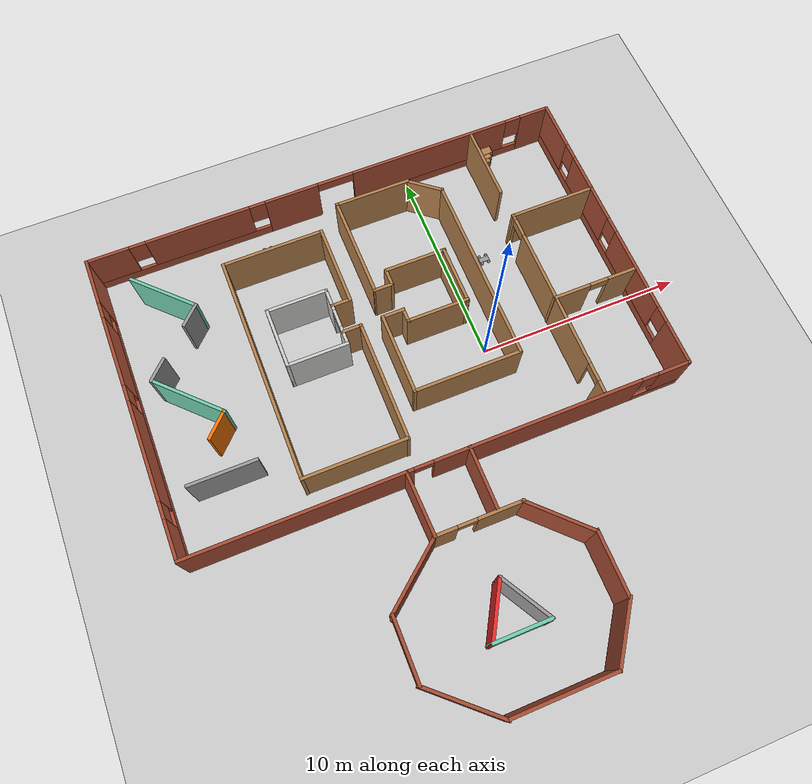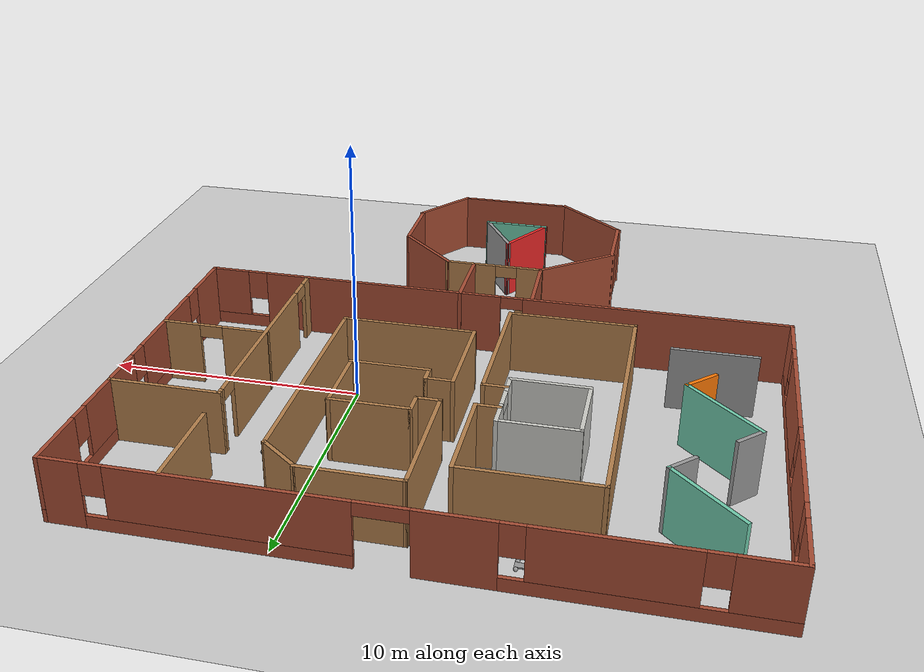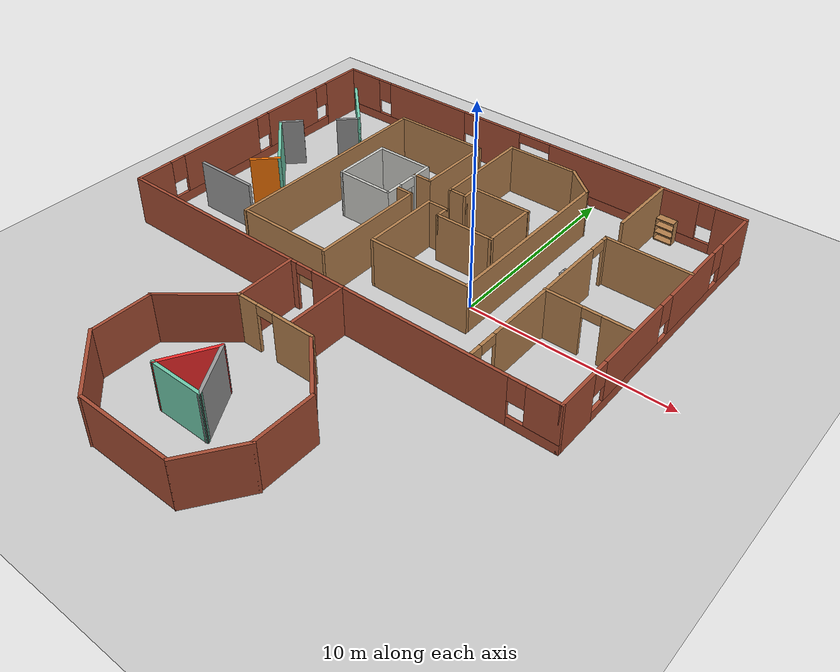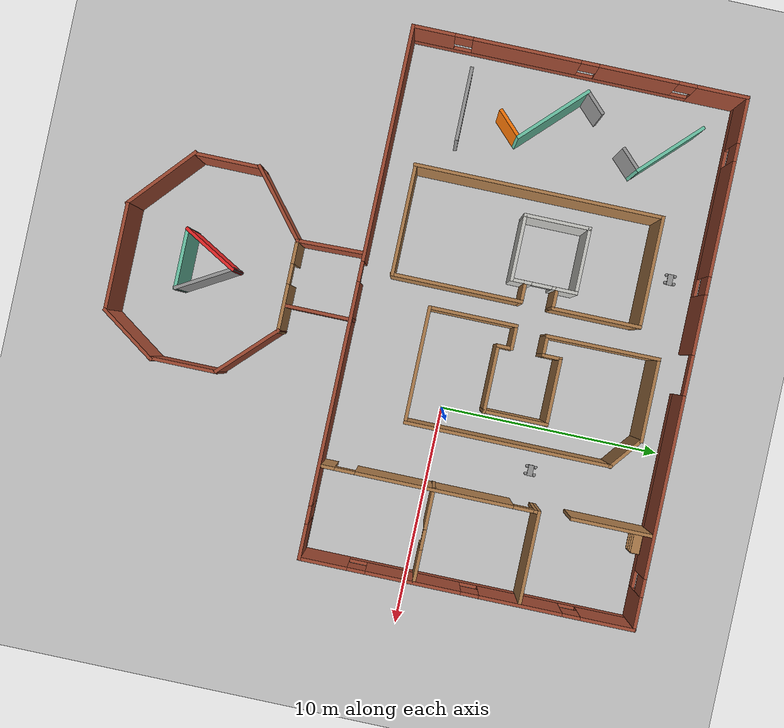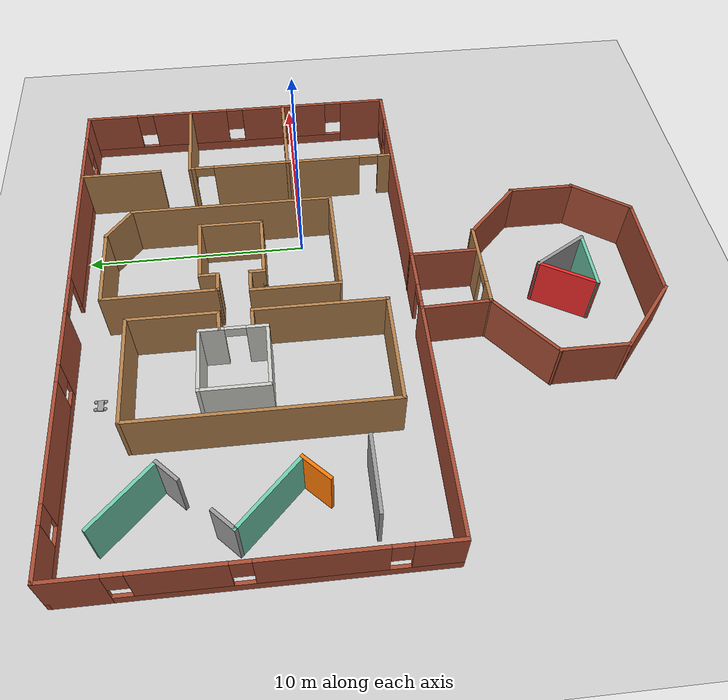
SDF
<sdf version="1.7">
 <world name="default">
  <plugin name="welcome" filename="libwelcome.so"/>
  <light name="sun" type="directional">
   <pose>0 0 10 0 -0 0</pose>
   <diffuse>0.8 0.8 0.8 1</diffuse>
   <specular>0.2 0.2 0.2 1</specular>
   <attenuation>
    <range>1000</range>
    <constant>0.9</constant>
    <linear>0.01</linear>
    <quadratic>0.001</quadratic>
   </attenuation>
   <direction>-0.5 0.1 -0.9</direction>
   <spot><inner_angle>0</inner_angle><outer_angle>0</outer_angle><falloff>0</falloff></spot>
  </light>
  <model name="ground_plane">
   <static>1</static>
   <link name="linkgp">
    <collision name="collision">
     <geometry><plane><normal>0 0 1</normal><size>100 100</size></plane></geometry>
     <surface>
      <contact><collide_bitmask>65535</collide_bitmask></contact>
      <friction><ode><mu>100</mu><mu2>50</mu2></ode></friction>
     </surface>
    </collision>
    <visual name="visual">
     <cast_shadows>0</cast_shadows>
     <geometry><plane><normal>0 0 1</normal><size>100 100</size></plane></geometry>
     <material>
      <script><uri>file://media/materials/scripts/gazebo.material</uri><name>Gazebo/Grey</name></script>
     </material>
    </visual>
   </link>
  </model>
  <gravity>0 0 -9.8</gravity>
  <magnetic_field>6e-06 2.3e-05 -4.2e-05</magnetic_field>
  <atmosphere type="adiabatic"/>
  <physics type="ode">
   <max_step_size>0.001</max_step_size>
   <real_time_factor>1</real_time_factor>
   <real_time_update_rate>1000</real_time_update_rate>
  </physics>
  <scene><ambient>0.4 0.4 0.4 1</ambient><background>0.7 0.7 0.7 1</background><shadows>1</shadows></scene>
  <spherical_coordinates>
   <surface_model>EARTH_WGS84</surface_model>
   <latitude_deg>0</latitude_deg>
   <longitude_deg>0</longitude_deg>
   <elevation>0</elevation>
   <heading_deg>0</heading_deg>
  </spherical_coordinates>
  <model name="RoboHab">
   <pose>-4.21544 -2.56056 0 0 -0 0</pose>
   <link name="Wall_19">
    <collision name="Wall_19_Collision">
     <geometry><box><size>3 0.15 2.5</size></box></geometry>
     <pose>0 0 1.25 0 -0 0</pose>
    </collision>
    <visual name="Wall_19_Visual">
     <pose>0 0 1.25 0 -0 0</pose>
     <geometry><box><size>3 0.15 2.5</size></box></geometry>
     <material>
      <script><uri>file://media/materials/scripts/gazebo.material</uri><name>Gazebo/CeilingTiled</name></script>
      <ambient>1 1 1 1</ambient>
     </material>
     <meta><layer>0</layer></meta>
    </visual>
    <pose>-4.80994 5.75548 0 0 -0 -1.5708</pose>
   </link>
   <link name="Wall_20">
    <collision name="Wall_20_Collision">
     <geometry><box><size>3 0.15 2.5</size></box></geometry>
     <pose>0 0 1.25 0 -0 0</pose>
    </collision>
    <visual name="Wall_20_Visual">
     <pose>0 0 1.25 0 -0 0</pose>
     <geometry><box><size>3 0.15 2.5</size></box></geometry>
     <material>
      <script><uri>file://media/materials/scripts/gazebo.material</uri><name>Gazebo/CeilingTiled</name></script>
      <ambient>1 1 1 1</ambient>
     </material>
     <meta><layer>0</layer></meta>
    </visual>
    <pose>-3.38494 4.33048 0 0 -0 0</pose>
   </link>
   <link name="Wall_21">
    <pose>-1.95993 5.75548 0 0 -0 1.5708</pose>
    <visual name="Wall_21_Visual_0">
     <pose>-1.02117 0 1.25 0 -0 0</pose>
     <geometry><box><size>0.957653 0.15 2.5</size></box></geometry>
     <material>
      <script><uri>file://media/materials/scripts/gazebo.material</uri><name>Gazebo/CeilingTiled</name></script>
      <ambient>1 1 1 1</ambient>
     </material>
     <meta><layer>0</layer></meta>
    </visual>
    <collision name="Wall_21_Collision_0">
     <geometry><box><size>0.957653 0.15 2.5</size></box></geometry>
     <pose>-1.02117 0 1.25 0 -0 0</pose>
    </collision>
    <visual name="Wall_21_Visual_1">
     <pose>0.928826 0 1.25 0 -0 0</pose>
     <geometry><box><size>1.14235 0.15 2.5</size></box></geometry>
     <material>
      <script><uri>file://media/materials/scripts/gazebo.material</uri><name>Gazebo/CeilingTiled</name></script>
      <ambient>1 1 1 1</ambient>
     </material>
     <meta><layer>0</layer></meta>
    </visual>
    <collision name="Wall_21_Collision_1">
     <geometry><box><size>1.14235 0.15 2.5</size></box></geometry>
     <pose>0.928826 0 1.25 0 -0 0</pose>
    </collision>
    <visual name="Wall_21_Visual_2">
     <pose>-0.092347 0 2.25 0 -0 0</pose>
     <geometry><box><size>0.9 0.15 0.5</size></box></geometry>
     <material>
      <script><uri>file://media/materials/scripts/gazebo.material</uri><name>Gazebo/CeilingTiled</name></script>
      <ambient>1 1 1 1</ambient>
     </material>
     <meta><layer>0</layer></meta>
    </visual>
    <collision name="Wall_21_Collision_2">
     <geometry><box><size>0.9 0.15 0.5</size></box></geometry>
     <pose>-0.092347 0 2.25 0 -0 0</pose>
    </collision>
   </link>
   <link name="Wall_22">
    <collision name="Wall_22_Collision">
     <geometry><box><size>3 0.15 2.5</size></box></geometry>
     <pose>0 0 1.25 0 -0 0</pose>
    </collision>
    <visual name="Wall_22_Visual">
     <pose>0 0 1.25 0 -0 0</pose>
     <geometry><box><size>3 0.15 2.5</size></box></geometry>
     <material>
      <script><uri>file://media/materials/scripts/gazebo.material</uri><name>Gazebo/CeilingTiled</name></script>
      <ambient>1 1 1 1</ambient>
     </material>
     <meta><layer>0</layer></meta>
    </visual>
    <pose>-3.38494 7.18048 0 0 -0 3.14159</pose>
   </link>
   <link name="Wall_24">
    <collision name="Wall_24_Collision">
     <geometry><box><size>1 0.15 2.5</size></box></geometry>
     <pose>0 0 1.25 0 -0 0</pose>
    </collision>
    <visual name="Wall_24_Visual">
     <pose>0 0 1.25 0 -0 0</pose>
     <geometry><box><size>1 0.15 2.5</size></box></geometry>
     <material>
      <script><uri>file://media/materials/scripts/gazebo.material</uri><name>Gazebo/Wood</name></script>
      <ambient>1 1 1 1</ambient>
     </material>
     <meta><layer>0</layer></meta>
    </visual>
    <pose>-1.52111 6.33992 0 0 -0 0</pose>
   </link>
   <link name="Wall_25">
    <collision name="Wall_25_Collision">
     <geometry><box><size>4 0.15 2.5</size></box></geometry>
     <pose>0 0 1.25 0 -0 0</pose>
    </collision>
    <visual name="Wall_25_Visual">
     <pose>0 0 1.25 0 -0 0</pose>
     <geometry><box><size>4 0.15 2.5</size></box></geometry>
     <material>
      <script><uri>file://media/materials/scripts/gazebo.material</uri><name>Gazebo/Wood</name></script>
      <ambient>1 1 1 1</ambient>
     </material>
     <meta><layer>0</layer></meta>
    </visual>
    <pose>-1.09611 8.26492 0 0 -0 1.5708</pose>
   </link>
   <link name="Wall_26">
    <collision name="Wall_26_Collision">
     <geometry><box><size>5 0.15 2.5</size></box></geometry>
     <pose>0 0 1.25 0 -0 0</pose>
    </collision>
    <visual name="Wall_26_Visual">
     <pose>0 0 1.25 0 -0 0</pose>
     <geometry><box><size>5 0.15 2.5</size></box></geometry>
     <material>
      <script><uri>file://media/materials/scripts/gazebo.material</uri><name>Gazebo/Wood</name></script>
      <ambient>1 1 1 1</ambient>
     </material>
     <meta><layer>0</layer></meta>
    </visual>
    <pose>-3.52111 10.1899 0 0 -0 3.14159</pose>
   </link>
   <link name="Wall_27">
    <collision name="Wall_27_Collision">
     <geometry><box><size>11.1467 0.15 2.5</size></box></geometry>
     <pose>0 0 1.25 0 -0 0</pose>
    </collision>
    <visual name="Wall_27_Visual">
     <pose>0 0 1.25 0 -0 0</pose>
     <geometry><box><size>11.1467 0.15 2.5</size></box></geometry>
     <material>
      <script><uri>file://media/materials/scripts/gazebo.material</uri><name>Gazebo/Wood</name></script>
      <ambient>1 1 1 1</ambient>
     </material>
     <meta><layer>0</layer></meta>
    </visual>
    <pose>-5.94611 4.69157 0 0 -0 -1.5708</pose>
   </link>
   <link name="Wall_28">
    <collision name="Wall_28_Collision">
     <geometry><box><size>5 0.15 2.5</size></box></geometry>
     <pose>0 0 1.25 0 -0 0</pose>
    </collision>
    <visual name="Wall_28_Visual">
     <pose>0 0 1.25 0 -0 0</pose>
     <geometry><box><size>5 0.15 2.5</size></box></geometry>
     <material>
      <script><uri>file://media/materials/scripts/gazebo.material</uri><name>Gazebo/Wood</name></script>
      <ambient>1 1 1 1</ambient>
     </material>
     <meta><layer>0</layer></meta>
    </visual>
    <pose>-3.52111 -0.783657 0 0 -0 0</pose>
   </link>
   <link name="Wall_29">
    <collision name="Wall_29_Collision">
     <geometry><box><size>5.89671 0.15 2.5</size></box></geometry>
     <pose>0 0 1.25 0 -0 0</pose>
    </collision>
    <visual name="Wall_29_Visual">
     <pose>0 0 1.25 0 -0 0</pose>
     <geometry><box><size>5.89671 0.15 2.5</size></box></geometry>
     <material>
      <script><uri>file://media/materials/scripts/gazebo.material</uri><name>Gazebo/Wood</name></script>
      <ambient>1 1 1 1</ambient>
     </material>
     <meta><layer>0</layer></meta>
    </visual>
    <pose>-1.09611 2.06657 0 0 -0 1.5708</pose>
   </link>
   <link name="Wall_30">
    <collision name="Wall_30_Collision">
     <geometry><box><size>1 0.15 2.5</size></box></geometry>
     <pose>0 0 1.25 0 -0 0</pose>
    </collision>
    <visual name="Wall_30_Visual">
     <pose>0 0 1.25 0 -0 0</pose>
     <geometry><box><size>1 0.15 2.5</size></box></geometry>
     <material>
      <script><uri>file://media/materials/scripts/gazebo.material</uri><name>Gazebo/Wood</name></script>
      <ambient>1 1 1 1</ambient>
     </material>
     <meta><layer>0</layer></meta>
    </visual>
    <pose>-1.52111 4.93992 0 0 -0 3.14159</pose>
   </link>
   <link name="Wall_32">
    <collision name="Wall_32_Collision">
     <geometry><box><size>1 0.15 2.5</size></box></geometry>
     <pose>0 0 1.25 0 -0 0</pose>
    </collision>
    <visual name="Wall_32_Visual">
     <pose>0 0 1.25 0 -0 0</pose>
     <geometry><box><size>1 0.15 2.5</size></box></geometry>
     <material>
      <script><uri>file://media/materials/scripts/gazebo.material</uri><name>Gazebo/Wood</name></script>
      <ambient>1 1 1 1</ambient>
     </material>
     <meta><layer>0</layer></meta>
    </visual>
    <pose>0.547275 4.95593 0 0 -0 0</pose>
   </link>
   <link name="Wall_33">
    <collision name="Wall_33_Collision">
     <geometry><box><size>0.75 0.15 2.5</size></box></geometry>
     <pose>0 0 1.25 0 -0 0</pose>
    </collision>
    <visual name="Wall_33_Visual">
     <pose>0 0 1.25 0 -0 0</pose>
     <geometry><box><size>0.75 0.15 2.5</size></box></geometry>
     <material>
      <script><uri>file://media/materials/scripts/gazebo.material</uri><name>Gazebo/Wood</name></script>
      <ambient>1 1 1 1</ambient>
     </material>
     <meta><layer>0</layer></meta>
    </visual>
    <pose>0.972275 4.65593 0 0 -0 -1.5708</pose>
   </link>
   <link name="Wall_34">
    <collision name="Wall_34_Collision">
     <geometry><box><size>3.08045 0.15 2.5</size></box></geometry>
     <pose>0 0 1.25 0 -0 0</pose>
    </collision>
    <visual name="Wall_34_Visual">
     <pose>0 0 1.25 0 -0 0</pose>
     <geometry><box><size>3.08045 0.15 2.5</size></box></geometry>
     <material>
      <script><uri>file://media/materials/scripts/gazebo.material</uri><name>Gazebo/Wood</name></script>
      <ambient>1 1 1 1</ambient>
     </material>
     <meta><layer>0</layer></meta>
    </visual>
    <pose>2.4375 4.35593 0 0 -0 0</pose>
   </link>
   <link name="Wall_35">
    <collision name="Wall_35_Collision">
     <geometry><box><size>2.91863 0.15 2.5</size></box></geometry>
     <pose>0 0 1.25 0 -0 0</pose>
    </collision>
    <visual name="Wall_35_Visual">
     <pose>0 0 1.25 0 -0 0</pose>
     <geometry><box><size>2.91863 0.15 2.5</size></box></geometry>
     <material>
      <script><uri>file://media/materials/scripts/gazebo.material</uri><name>Gazebo/Wood</name></script>
      <ambient>1 1 1 1</ambient>
     </material>
     <meta><layer>0</layer></meta>
    </visual>
    <pose>3.88262 5.74024 0 0 -0 1.5708</pose>
   </link>
   <link name="Wall_36">
    <collision name="Wall_36_Collision">
     <geometry><box><size>2.99908 0.15 2.5</size></box></geometry>
     <pose>0 0 1.25 0 -0 0</pose>
    </collision>
    <visual name="Wall_36_Visual">
     <pose>0 0 1.25 0 -0 0</pose>
     <geometry><box><size>2.99908 0.15 2.5</size></box></geometry>
     <material>
      <script><uri>file://media/materials/scripts/gazebo.material</uri><name>Gazebo/Wood</name></script>
      <ambient>1 1 1 1</ambient>
     </material>
     <meta><layer>0</layer></meta>
    </visual>
    <pose>2.47819 7.12455 0 0 -0 3.14159</pose>
   </link>
   <link name="Wall_37">
    <collision name="Wall_37_Collision">
     <geometry><box><size>0.918629 0.15 2.5</size></box></geometry>
     <pose>0 0 1.25 0 -0 0</pose>
    </collision>
    <visual name="Wall_37_Visual">
     <pose>0 0 1.25 0 -0 0</pose>
     <geometry><box><size>0.918629 0.15 2.5</size></box></geometry>
     <material>
      <script><uri>file://media/materials/scripts/gazebo.material</uri><name>Gazebo/Wood</name></script>
      <ambient>1 1 1 1</ambient>
     </material>
     <meta><layer>0</layer></meta>
    </visual>
    <pose>0.972275 6.74024 0 0 -0 -1.5708</pose>
   </link>
   <link name="Wall_38">
    <collision name="Wall_38_Collision">
     <geometry><box><size>1 0.15 2.5</size></box></geometry>
     <pose>0 0 1.25 0 -0 0</pose>
    </collision>
    <visual name="Wall_38_Visual">
     <pose>0 0 1.25 0 -0 0</pose>
     <geometry><box><size>1 0.15 2.5</size></box></geometry>
     <material>
      <script><uri>file://media/materials/scripts/gazebo.material</uri><name>Gazebo/Wood</name></script>
      <ambient>1 1 1 1</ambient>
     </material>
     <meta><layer>0</layer></meta>
    </visual>
    <pose>0.547275 6.35593 0 0 -0 3.14159</pose>
   </link>
   <link name="Wall_39">
    <collision name="Wall_39_Collision">
     <geometry><box><size>5.09068 0.15 2.5</size></box></geometry>
     <pose>0 0 1.25 0 -0 0</pose>
    </collision>
    <visual name="Wall_39_Visual">
     <pose>0 0 1.25 0 -0 0</pose>
     <geometry><box><size>5.09068 0.15 2.5</size></box></geometry>
     <material>
      <script><uri>file://media/materials/scripts/gazebo.material</uri><name>Gazebo/Wood</name></script>
      <ambient>1 1 1 1</ambient>
     </material>
     <meta><layer>0</layer></meta>
    </visual>
    <pose>0.108975 8.82623 0 0 -0 1.57618</pose>
   </link>
   <link name="Wall_40">
    <collision name="Wall_40_Collision">
     <geometry><box><size>3.75 0.15 2.5</size></box></geometry>
     <pose>0 0 1.25 0 -0 0</pose>
    </collision>
    <visual name="Wall_40_Visual">
     <pose>0 0 1.25 0 -0 0</pose>
     <geometry><box><size>3.75 0.15 2.5</size></box></geometry>
     <material>
      <script><uri>file://media/materials/scripts/gazebo.material</uri><name>Gazebo/Wood</name></script>
      <ambient>1 1 1 1</ambient>
     </material>
     <meta><layer>0</layer></meta>
    </visual>
    <pose>1.92227 11.2965 0 0 -0 0</pose>
   </link>
   <link name="Wall_41">
    <collision name="Wall_41_Collision">
     <geometry><box><size>1.90626 0.15 2.5</size></box></geometry>
     <pose>0 0 1.25 0 -0 0</pose>
    </collision>
    <visual name="Wall_41_Visual">
     <pose>0 0 1.25 0 -0 0</pose>
     <geometry><box><size>1.90626 0.15 2.5</size></box></geometry>
     <material>
      <script><uri>file://media/materials/scripts/gazebo.material</uri><name>Gazebo/Wood</name></script>
      <ambient>1 1 1 1</ambient>
     </material>
     <meta><layer>0</layer></meta>
    </visual>
    <pose>4.38398 10.7512 0 0 -0 -0.669996</pose>
   </link>
   <link name="Wall_42">
    <collision name="Wall_42_Collision">
     <geometry><box><size>9.25 0.15 2.5</size></box></geometry>
     <pose>0 0 1.25 0 -0 0</pose>
    </collision>
    <visual name="Wall_42_Visual">
     <pose>0 0 1.25 0 -0 0</pose>
     <geometry><box><size>9.25 0.15 2.5</size></box></geometry>
     <material>
      <script><uri>file://media/materials/scripts/gazebo.material</uri><name>Gazebo/Wood</name></script>
      <ambient>1 1 1 1</ambient>
     </material>
     <meta><layer>0</layer></meta>
    </visual>
    <pose>5.07228 5.65593 0 0 -0 -1.5708</pose>
   </link>
   <link name="Wall_43">
    <collision name="Wall_43_Collision">
     <geometry><box><size>5.25 0.15 2.5</size></box></geometry>
     <pose>0 0 1.25 0 -0 0</pose>
    </collision>
    <visual name="Wall_43_Visual">
     <pose>0 0 1.25 0 -0 0</pose>
     <geometry><box><size>5.25 0.15 2.5</size></box></geometry>
     <material>
      <script><uri>file://media/materials/scripts/gazebo.material</uri><name>Gazebo/Wood</name></script>
      <ambient>1 1 1 1</ambient>
     </material>
     <meta><layer>0</layer></meta>
    </visual>
    <pose>2.52228 1.10593 0 0 -0 3.14159</pose>
   </link>
   <link name="Wall_44">
    <collision name="Wall_44_Collision">
     <geometry><box><size>4 0.15 2.5</size></box></geometry>
     <pose>0 0 1.25 0 -0 0</pose>
    </collision>
    <visual name="Wall_44_Visual">
     <pose>0 0 1.25 0 -0 0</pose>
     <geometry><box><size>4 0.15 2.5</size></box></geometry>
     <material>
      <script><uri>file://media/materials/scripts/gazebo.material</uri><name>Gazebo/Wood</name></script>
      <ambient>1 1 1 1</ambient>
     </material>
     <meta><layer>0</layer></meta>
    </visual>
    <pose>-0.027725 3.03093 0 0 -0 1.5708</pose>
   </link>
   <link name="Wall_46">
    <pose>-11.8 5.2719 0 0 -0 -1.5708</pose>
    <visual name="Wall_46_Visual_0">
     <pose>-6.33247 0 1.25 0 -0 0</pose>
     <geometry><box><size>2.33506 0.15 2.5</size></box></geometry>
     <material>
      <script><uri>file://media/materials/scripts/gazebo.material</uri><name>Gazebo/Bricks</name></script>
      <ambient>1 1 1 1</ambient>
     </material>
     <meta><layer>0</layer></meta>
    </visual>
    <collision name="Wall_46_Collision_0">
     <geometry><box><size>2.33506 0.15 2.5</size></box></geometry>
     <pose>-6.33247 0 1.25 0 -0 0</pose>
    </collision>
    <visual name="Wall_46_Visual_1">
     <pose>1.16753 0 0.25 0 -0 0</pose>
     <geometry><box><size>12.6649 0.15 0.5</size></box></geometry>
     <material>
      <script><uri>file://media/materials/scripts/gazebo.material</uri><name>Gazebo/Bricks</name></script>
      <ambient>1 1 1 1</ambient>
     </material>
     <meta><layer>0</layer></meta>
    </visual>
    <collision name="Wall_46_Collision_1">
     <geometry><box><size>12.6649 0.15 0.5</size></box></geometry>
     <pose>1.16753 0 0.25 0 -0 0</pose>
    </collision>
    <visual name="Wall_46_Visual_2">
     <pose>-2.60145 0 1.5 0 -0 0</pose>
     <geometry><box><size>3.52699 0.15 2</size></box></geometry>
     <material>
      <script><uri>file://media/materials/scripts/gazebo.material</uri><name>Gazebo/Bricks</name></script>
      <ambient>1 1 1 1</ambient>
     </material>
     <meta><layer>0</layer></meta>
    </visual>
    <collision name="Wall_46_Collision_2">
     <geometry><box><size>3.52699 0.15 2</size></box></geometry>
     <pose>-2.60145 0 1.5 0 -0 0</pose>
    </collision>
    <visual name="Wall_46_Visual_3">
     <pose>2.35876 0 1.5 0 -0 0</pose>
     <geometry><box><size>4.79342 0.15 2</size></box></geometry>
     <material>
      <script><uri>file://media/materials/scripts/gazebo.material</uri><name>Gazebo/Bricks</name></script>
      <ambient>1 1 1 1</ambient>
     </material>
     <meta><layer>0</layer></meta>
    </visual>
    <collision name="Wall_46_Collision_3">
     <geometry><box><size>4.79342 0.15 2</size></box></geometry>
     <pose>2.35876 0 1.5 0 -0 0</pose>
    </collision>
    <visual name="Wall_46_Visual_4">
     <pose>6.52773 0 1.5 0 -0 0</pose>
     <geometry><box><size>1.94453 0.15 2</size></box></geometry>
     <material>
      <script><uri>file://media/materials/scripts/gazebo.material</uri><name>Gazebo/Bricks</name></script>
      <ambient>1 1 1 1</ambient>
     </material>
     <meta><layer>0</layer></meta>
    </visual>
    <collision name="Wall_46_Collision_4">
     <geometry><box><size>1.94453 0.15 2</size></box></geometry>
     <pose>6.52773 0 1.5 0 -0 0</pose>
    </collision>
    <visual name="Wall_46_Visual_5">
     <pose>-4.76494 0 1.9 0 -0 0</pose>
     <geometry><box><size>0.8 0.15 1.2</size></box></geometry>
     <material>
      <script><uri>file://media/materials/scripts/gazebo.material</uri><name>Gazebo/Bricks</name></script>
      <ambient>1 1 1 1</ambient>
     </material>
     <meta><layer>0</layer></meta>
    </visual>
    <collision name="Wall_46_Collision_5">
     <geometry><box><size>0.8 0.15 1.2</size></box></geometry>
     <pose>-4.76494 0 1.9 0 -0 0</pose>
    </collision>
    <visual name="Wall_46_Visual_6">
     <pose>-0.437953 0 1.9 0 -0 0</pose>
     <geometry><box><size>0.8 0.15 1.2</size></box></geometry>
     <material>
      <script><uri>file://media/materials/scripts/gazebo.material</uri><name>Gazebo/Bricks</name></script>
      <ambient>1 1 1 1</ambient>
     </material>
     <meta><layer>0</layer></meta>
    </visual>
    <collision name="Wall_46_Collision_6">
     <geometry><box><size>0.8 0.15 1.2</size></box></geometry>
     <pose>-0.437953 0 1.9 0 -0 0</pose>
    </collision>
    <visual name="Wall_46_Visual_7">
     <pose>5.15547 0 1.9 0 -0 0</pose>
     <geometry><box><size>0.8 0.15 1.2</size></box></geometry>
     <material>
      <script><uri>file://media/materials/scripts/gazebo.material</uri><name>Gazebo/Bricks</name></script>
      <ambient>1 1 1 1</ambient>
     </material>
     <meta><layer>0</layer></meta>
    </visual>
    <collision name="Wall_46_Collision_7">
     <geometry><box><size>0.8 0.15 1.2</size></box></geometry>
     <pose>5.15547 0 1.9 0 -0 0</pose>
    </collision>
   </link>
   <link name="Wall_47">
    <pose>-0 -2.1531 0 0 -0 0</pose>
    <visual name="Wall_47_Visual_0">
     <pose>-6.62427 0 1.25 0 -0 0</pose>
     <geometry><box><size>10.5015 0.15 2.5</size></box></geometry>
     <material>
      <script><uri>file://media/materials/scripts/gazebo.material</uri><name>Gazebo/Bricks</name></script>
      <ambient>1 1 1 1</ambient>
     </material>
     <meta><layer>0</layer></meta>
    </visual>
    <collision name="Wall_47_Collision_0">
     <geometry><box><size>10.5015 0.15 2.5</size></box></geometry>
     <pose>-6.62427 0 1.25 0 -0 0</pose>
    </collision>
    <visual name="Wall_47_Visual_1">
     <pose>4.49789 0 1.25 0 -0 0</pose>
     <geometry><box><size>9.94287 0.15 2.5</size></box></geometry>
     <material>
      <script><uri>file://media/materials/scripts/gazebo.material</uri><name>Gazebo/Bricks</name></script>
      <ambient>1 1 1 1</ambient>
     </material>
     <meta><layer>0</layer></meta>
    </visual>
    <collision name="Wall_47_Collision_1">
     <geometry><box><size>9.94287 0.15 2.5</size></box></geometry>
     <pose>4.49789 0 1.25 0 -0 0</pose>
    </collision>
    <visual name="Wall_47_Visual_2">
     <pose>10.6722 0 0.25 0 -0 0</pose>
     <geometry><box><size>2.40568 0.15 0.5</size></box></geometry>
     <material>
      <script><uri>file://media/materials/scripts/gazebo.material</uri><name>Gazebo/Bricks</name></script>
      <ambient>1 1 1 1</ambient>
     </material>
     <meta><layer>0</layer></meta>
    </visual>
    <collision name="Wall_47_Collision_2">
     <geometry><box><size>2.40568 0.15 0.5</size></box></geometry>
     <pose>10.6722 0 0.25 0 -0 0</pose>
    </collision>
    <visual name="Wall_47_Visual_3">
     <pose>11.0722 0 1.5 0 -0 0</pose>
     <geometry><box><size>1.60568 0.15 2</size></box></geometry>
     <material>
      <script><uri>file://media/materials/scripts/gazebo.material</uri><name>Gazebo/Bricks</name></script>
      <ambient>1 1 1 1</ambient>
     </material>
     <meta><layer>0</layer></meta>
    </visual>
    <collision name="Wall_47_Collision_3">
     <geometry><box><size>1.60568 0.15 2</size></box></geometry>
     <pose>11.0722 0 1.5 0 -0 0</pose>
    </collision>
    <visual name="Wall_47_Visual_4">
     <pose>9.86932 0 1.9 0 -0 0</pose>
     <geometry><box><size>0.8 0.15 1.2</size></box></geometry>
     <material>
      <script><uri>file://media/materials/scripts/gazebo.material</uri><name>Gazebo/Bricks</name></script>
      <ambient>1 1 1 1</ambient>
     </material>
     <meta><layer>0</layer></meta>
    </visual>
    <collision name="Wall_47_Collision_4">
     <geometry><box><size>0.8 0.15 1.2</size></box></geometry>
     <pose>9.86932 0 1.9 0 -0 0</pose>
    </collision>
    <visual name="Wall_47_Visual_5">
     <pose>-0.923549 0 2.25 0 -0 0</pose>
     <geometry><box><size>0.9 0.15 0.5</size></box></geometry>
     <material>
      <script><uri>file://media/materials/scripts/gazebo.material</uri><name>Gazebo/Bricks</name></script>
      <ambient>1 1 1 1</ambient>
     </material>
     <meta><layer>0</layer></meta>
    </visual>
    <collision name="Wall_47_Collision_5">
     <geometry><box><size>0.9 0.15 0.5</size></box></geometry>
     <pose>-0.923549 0 2.25 0 -0 0</pose>
    </collision>
   </link>
   <link name="Wall_48">
    <pose>11.8 5.2719 0 0 -0 1.5708</pose>
    <visual name="Wall_48_Visual_0">
     <pose>-6.40461 0 1.25 0 -0 0</pose>
     <geometry><box><size>2.19078 0.15 2.5</size></box></geometry>
     <material>
      <script><uri>file://media/materials/scripts/gazebo.material</uri><name>Gazebo/Bricks</name></script>
      <ambient>1 1 1 1</ambient>
     </material>
     <meta><layer>0</layer></meta>
    </visual>
    <collision name="Wall_48_Collision_0">
     <geometry><box><size>2.19078 0.15 2.5</size></box></geometry>
     <pose>-6.40461 0 1.25 0 -0 0</pose>
    </collision>
    <visual name="Wall_48_Visual_1">
     <pose>1.09539 0 0.25 0 -0 0</pose>
     <geometry><box><size>12.8092 0.15 0.5</size></box></geometry>
     <material>
      <script><uri>file://media/materials/scripts/gazebo.material</uri><name>Gazebo/Bricks</name></script>
      <ambient>1 1 1 1</ambient>
     </material>
     <meta><layer>0</layer></meta>
    </visual>
    <collision name="Wall_48_Collision_1">
     <geometry><box><size>12.8092 0.15 0.5</size></box></geometry>
     <pose>1.09539 0 0.25 0 -0 0</pose>
    </collision>
    <visual name="Wall_48_Visual_2">
     <pose>-2.39394 0 1.5 0 -0 0</pose>
     <geometry><box><size>4.23056 0.15 2</size></box></geometry>
     <material>
      <script><uri>file://media/materials/scripts/gazebo.material</uri><name>Gazebo/Bricks</name></script>
      <ambient>1 1 1 1</ambient>
     </material>
     <meta><layer>0</layer></meta>
    </visual>
    <collision name="Wall_48_Collision_2">
     <geometry><box><size>4.23056 0.15 2</size></box></geometry>
     <pose>-2.39394 0 1.5 0 -0 0</pose>
    </collision>
    <visual name="Wall_48_Visual_3">
     <pose>2.37278 0 1.5 0 -0 0</pose>
     <geometry><box><size>3.70288 0.15 2</size></box></geometry>
     <material>
      <script><uri>file://media/materials/scripts/gazebo.material</uri><name>Gazebo/Bricks</name></script>
      <ambient>1 1 1 1</ambient>
     </material>
     <meta><layer>0</layer></meta>
    </visual>
    <collision name="Wall_48_Collision_3">
     <geometry><box><size>3.70288 0.15 2</size></box></geometry>
     <pose>2.37278 0 1.5 0 -0 0</pose>
    </collision>
    <visual name="Wall_48_Visual_4">
     <pose>6.26211 0 1.5 0 -0 0</pose>
     <geometry><box><size>2.47577 0.15 2</size></box></geometry>
     <material>
      <script><uri>file://media/materials/scripts/gazebo.material</uri><name>Gazebo/Bricks</name></script>
      <ambient>1 1 1 1</ambient>
     </material>
     <meta><layer>0</layer></meta>
    </visual>
    <collision name="Wall_48_Collision_4">
     <geometry><box><size>2.47577 0.15 2</size></box></geometry>
     <pose>6.26211 0 1.5 0 -0 0</pose>
    </collision>
    <visual name="Wall_48_Visual_5">
     <pose>-4.90922 0 1.9 0 -0 0</pose>
     <geometry><box><size>0.8 0.15 1.2</size></box></geometry>
     <material>
      <script><uri>file://media/materials/scripts/gazebo.material</uri><name>Gazebo/Bricks</name></script>
      <ambient>1 1 1 1</ambient>
     </material>
     <meta><layer>0</layer></meta>
    </visual>
    <collision name="Wall_48_Collision_5">
     <geometry><box><size>0.8 0.15 1.2</size></box></geometry>
     <pose>-4.90922 0 1.9 0 -0 0</pose>
    </collision>
    <visual name="Wall_48_Visual_6">
     <pose>0.121344 0 1.9 0 -0 0</pose>
     <geometry><box><size>0.8 0.15 1.2</size></box></geometry>
     <material>
      <script><uri>file://media/materials/scripts/gazebo.material</uri><name>Gazebo/Bricks</name></script>
      <ambient>1 1 1 1</ambient>
     </material>
     <meta><layer>0</layer></meta>
    </visual>
    <collision name="Wall_48_Collision_6">
     <geometry><box><size>0.8 0.15 1.2</size></box></geometry>
     <pose>0.121344 0 1.9 0 -0 0</pose>
    </collision>
    <visual name="Wall_48_Visual_7">
     <pose>4.62423 0 1.9 0 -0 0</pose>
     <geometry><box><size>0.8 0.15 1.2</size></box></geometry>
     <material>
      <script><uri>file://media/materials/scripts/gazebo.material</uri><name>Gazebo/Bricks</name></script>
      <ambient>1 1 1 1</ambient>
     </material>
     <meta><layer>0</layer></meta>
    </visual>
    <collision name="Wall_48_Collision_7">
     <geometry><box><size>0.8 0.15 1.2</size></box></geometry>
     <pose>4.62423 0 1.9 0 -0 0</pose>
    </collision>
   </link>
   <link name="Wall_49">
    <pose>-0 12.6969 0 0 -0 3.14159</pose>
    <visual name="Wall_49_Visual_0">
     <pose>-11.1073 0 1.25 0 -0 0</pose>
     <geometry><box><size>1.53532 0.15 2.5</size></box></geometry>
     <material>
      <script><uri>file://media/materials/scripts/gazebo.material</uri><name>Gazebo/Bricks</name></script>
      <ambient>1 1 1 1</ambient>
     </material>
     <meta><layer>0</layer></meta>
    </visual>
    <collision name="Wall_49_Collision_0">
     <geometry><box><size>1.53532 0.15 2.5</size></box></geometry>
     <pose>-11.1073 0 1.25 0 -0 0</pose>
    </collision>
    <visual name="Wall_49_Visual_1">
     <pose>1.72583 0 1.25 0 -0 0</pose>
     <geometry><box><size>2.6752 0.15 2.5</size></box></geometry>
     <material>
      <script><uri>file://media/materials/scripts/gazebo.material</uri><name>Gazebo/Bricks</name></script>
      <ambient>1 1 1 1</ambient>
     </material>
     <meta><layer>0</layer></meta>
    </visual>
    <collision name="Wall_49_Collision_1">
     <geometry><box><size>2.6752 0.15 2.5</size></box></geometry>
     <pose>1.72583 0 1.25 0 -0 0</pose>
    </collision>
    <visual name="Wall_49_Visual_2">
     <pose>-5.87573 0 0.25 0 -0 0</pose>
     <geometry><box><size>8.92791 0.15 0.5</size></box></geometry>
     <material>
      <script><uri>file://media/materials/scripts/gazebo.material</uri><name>Gazebo/Bricks</name></script>
      <ambient>1 1 1 1</ambient>
     </material>
     <meta><layer>0</layer></meta>
    </visual>
    <collision name="Wall_49_Collision_2">
     <geometry><box><size>8.92791 0.15 0.5</size></box></geometry>
     <pose>-5.87573 0 0.25 0 -0 0</pose>
    </collision>
    <visual name="Wall_49_Visual_3">
     <pose>7.46921 0 0.25 0 -0 0</pose>
     <geometry><box><size>8.81157 0.15 0.5</size></box></geometry>
     <material>
      <script><uri>file://media/materials/scripts/gazebo.material</uri><name>Gazebo/Bricks</name></script>
      <ambient>1 1 1 1</ambient>
     </material>
     <meta><layer>0</layer></meta>
    </visual>
    <collision name="Wall_49_Collision_3">
     <geometry><box><size>8.81157 0.15 0.5</size></box></geometry>
     <pose>7.46921 0 0.25 0 -0 0</pose>
    </collision>
    <visual name="Wall_49_Visual_4">
     <pose>-5.47573 0 1.5 0 -0 0</pose>
     <geometry><box><size>8.12791 0.15 2</size></box></geometry>
     <material>
      <script><uri>file://media/materials/scripts/gazebo.material</uri><name>Gazebo/Bricks</name></script>
      <ambient>1 1 1 1</ambient>
     </material>
     <meta><layer>0</layer></meta>
    </visual>
    <collision name="Wall_49_Collision_4">
     <geometry><box><size>8.12791 0.15 2</size></box></geometry>
     <pose>-5.47573 0 1.5 0 -0 0</pose>
    </collision>
    <visual name="Wall_49_Visual_5">
     <pose>-5.47573 0 1.5 0 -0 0</pose>
     <geometry><box><size>8.12791 0.15 2</size></box></geometry>
     <material>
      <script><uri>file://media/materials/scripts/gazebo.material</uri><name>Gazebo/Bricks</name></script>
      <ambient>1 1 1 1</ambient>
     </material>
     <meta><layer>0</layer></meta>
    </visual>
    <collision name="Wall_49_Collision_5">
     <geometry><box><size>8.12791 0.15 2</size></box></geometry>
     <pose>-5.47573 0 1.5 0 -0 0</pose>
    </collision>
    <visual name="Wall_49_Visual_6">
     <pose>6.41844 0 1.5 0 -0 0</pose>
     <geometry><box><size>5.11003 0.15 2</size></box></geometry>
     <material>
      <script><uri>file://media/materials/scripts/gazebo.material</uri><name>Gazebo/Bricks</name></script>
      <ambient>1 1 1 1</ambient>
     </material>
     <meta><layer>0</layer></meta>
    </visual>
    <collision name="Wall_49_Collision_6">
     <geometry><box><size>5.11003 0.15 2</size></box></geometry>
     <pose>6.41844 0 1.5 0 -0 0</pose>
    </collision>
    <visual name="Wall_49_Visual_7">
     <pose>10.8242 0 1.5 0 -0 0</pose>
     <geometry><box><size>2.10154 0.15 2</size></box></geometry>
     <material>
      <script><uri>file://media/materials/scripts/gazebo.material</uri><name>Gazebo/Bricks</name></script>
      <ambient>1 1 1 1</ambient>
     </material>
     <meta><layer>0</layer></meta>
    </visual>
    <collision name="Wall_49_Collision_7">
     <geometry><box><size>2.10154 0.15 2</size></box></geometry>
     <pose>10.8242 0 1.5 0 -0 0</pose>
    </collision>
    <visual name="Wall_49_Visual_8">
     <pose>-9.93968 0 1.9 0 -0 0</pose>
     <geometry><box><size>0.8 0.15 1.2</size></box></geometry>
     <material>
      <script><uri>file://media/materials/scripts/gazebo.material</uri><name>Gazebo/Bricks</name></script>
      <ambient>1 1 1 1</ambient>
     </material>
     <meta><layer>0</layer></meta>
    </visual>
    <collision name="Wall_49_Collision_8">
     <geometry><box><size>0.8 0.15 1.2</size></box></geometry>
     <pose>-9.93968 0 1.9 0 -0 0</pose>
    </collision>
    <visual name="Wall_49_Visual_9">
     <pose>3.46343 0 1.9 0 -0 0</pose>
     <geometry><box><size>0.8 0.15 1.2</size></box></geometry>
     <material>
      <script><uri>file://media/materials/scripts/gazebo.material</uri><name>Gazebo/Bricks</name></script>
      <ambient>1 1 1 1</ambient>
     </material>
     <meta><layer>0</layer></meta>
    </visual>
    <collision name="Wall_49_Collision_9">
     <geometry><box><size>0.8 0.15 1.2</size></box></geometry>
     <pose>3.46343 0 1.9 0 -0 0</pose>
    </collision>
    <visual name="Wall_49_Visual_10">
     <pose>9.37346 0 1.9 0 -0 0</pose>
     <geometry><box><size>0.8 0.15 1.2</size></box></geometry>
     <material>
      <script><uri>file://media/materials/scripts/gazebo.material</uri><name>Gazebo/Bricks</name></script>
      <ambient>1 1 1 1</ambient>
     </material>
     <meta><layer>0</layer></meta>
    </visual>
    <collision name="Wall_49_Collision_10">
     <geometry><box><size>0.8 0.15 1.2</size></box></geometry>
     <pose>9.37346 0 1.9 0 -0 0</pose>
    </collision>
    <visual name="Wall_49_Visual_11">
     <pose>-0.511773 0 2.25 0 -0 0</pose>
     <geometry><box><size>1.8 0.15 0.5</size></box></geometry>
     <material>
      <script><uri>file://media/materials/scripts/gazebo.material</uri><name>Gazebo/Bricks</name></script>
      <ambient>1 1 1 1</ambient>
     </material>
     <meta><layer>0</layer></meta>
    </visual>
    <collision name="Wall_49_Collision_11">
     <geometry><box><size>1.8 0.15 0.5</size></box></geometry>
     <pose>-0.511773 0 2.25 0 -0 0</pose>
    </collision>
    <visual name="Wall_49_Visual_12">
     <pose>-0.511773 0 2.25 0 -0 0</pose>
     <geometry><box><size>1.8 0.15 0.5</size></box></geometry>
     <material>
      <script><uri>file://media/materials/scripts/gazebo.material</uri><name>Gazebo/Bricks</name></script>
      <ambient>1 1 1 1</ambient>
     </material>
     <meta><layer>0</layer></meta>
    </visual>
    <collision name="Wall_49_Collision_12">
     <geometry><box><size>1.8 0.15 0.5</size></box></geometry>
     <pose>-0.511773 0 2.25 0 -0 0</pose>
    </collision>
   </link>
   <link name="Wall_51">
    <collision name="Wall_51_Collision">
     <geometry><box><size>3.5 0.15 2.5</size></box></geometry>
     <pose>0 0 1.25 0 -0 0</pose>
    </collision>
    <visual name="Wall_51_Visual">
     <pose>0 0 1.25 0 -0 0</pose>
     <geometry><box><size>3.5 0.15 2.5</size></box></geometry>
     <material>
      <script><uri>file://media/materials/scripts/gazebo.material</uri><name>Gazebo/Grey</name></script>
      <ambient>0.435294 0.796078 0.67451 1</ambient>
     </material>
     <meta><layer>0</layer></meta>
    </visual>
    <pose>-8.90916 9.88162 0 0 -0 -0.785398</pose>
   </link>
   <link name="Wall_52">
    <collision name="Wall_52_Collision">
     <geometry><box><size>1.25 0.15 2.5</size></box></geometry>
     <pose>0 0 1.25 0 -0 0</pose>
    </collision>
    <visual name="Wall_52_Visual">
     <pose>0 0 1.25 0 -0 0</pose>
     <geometry><box><size>1.25 0.15 2.5</size></box></geometry>
     <material>
      <script><uri>file://media/materials/scripts/gazebo.material</uri><name>Gazebo/Grey</name></script>
      <ambient>1 1 1 1</ambient>
     </material>
     <meta><layer>0</layer></meta>
    </visual>
    <pose>-8.11366 8.30831 0 0 -0 -2.35619</pose>
   </link>
   <link name="Wall_54">
    <collision name="Wall_54_Collision">
     <geometry><box><size>1.25 0.15 2.5</size></box></geometry>
     <pose>0 0 1.25 0 -0 0</pose>
    </collision>
    <visual name="Wall_54_Visual">
     <pose>0 0 1.25 0 -0 0</pose>
     <geometry><box><size>1.25 0.15 2.5</size></box></geometry>
     <material>
      <script><uri>file://media/materials/scripts/gazebo.material</uri><name>Gazebo/Grey</name></script>
      <ambient>1 1 1 1</ambient>
     </material>
     <meta><layer>0</layer></meta>
    </visual>
    <pose>-10.2165 6.26148 0 0 -0 -2.35619</pose>
   </link>
   <link name="Wall_55">
    <collision name="Wall_55_Collision">
     <geometry><box><size>3.75 0.15 2.5</size></box></geometry>
     <pose>0 0 1.25 0 -0 0</pose>
    </collision>
    <visual name="Wall_55_Visual">
     <pose>0 0 1.25 0 -0 0</pose>
     <geometry><box><size>3.75 0.15 2.5</size></box></geometry>
     <material>
      <script><uri>file://media/materials/scripts/gazebo.material</uri><name>Gazebo/Grey</name></script>
      <ambient>0.435294 0.796078 0.67451 1</ambient>
     </material>
     <meta><layer>0</layer></meta>
    </visual>
    <pose>-9.33258 4.59978 0 0 -0 -0.785398</pose>
   </link>
   <link name="Wall_56">
    <collision name="Wall_56_Collision">
     <geometry><box><size>1.5 0.15 2.5</size></box></geometry>
     <pose>0 0 1.25 0 -0 0</pose>
    </collision>
    <visual name="Wall_56_Visual">
     <pose>0 0 1.25 0 -0 0</pose>
     <geometry><box><size>1.5 0.15 2.5</size></box></geometry>
     <material>
      <script><uri>file://media/materials/scripts/gazebo.material</uri><name>Gazebo/Grey</name></script>
      <ambient>0.996078 0.47451 0.0196078 1</ambient>
     </material>
     <meta><layer>0</layer></meta>
    </visual>
    <pose>-8.53709 2.84969 0 0 -0 -2.35619</pose>
   </link>
   <link name="Wall_58">
    <collision name="Wall_58_Collision">
     <geometry><box><size>3.25 0.15 2.5</size></box></geometry>
     <pose>0 0 1.25 0 -0 0</pose>
    </collision>
    <visual name="Wall_58_Visual">
     <pose>0 0 1.25 0 -0 0</pose>
     <geometry><box><size>3.25 0.15 2.5</size></box></geometry>
     <material>
      <script><uri>file://media/materials/scripts/gazebo.material</uri><name>Gazebo/Grey</name></script>
      <ambient>1 1 1 1</ambient>
     </material>
     <meta><layer>0</layer></meta>
    </visual>
    <pose>-8.96916 0.718549 0 0 -0 0</pose>
   </link>
   <link name="Wall_60">
    <collision name="Wall_60_Collision">
     <geometry><box><size>3.75 0.15 2.5</size></box></geometry>
     <pose>0 0 1.25 0 -0 0</pose>
    </collision>
    <visual name="Wall_60_Visual">
     <pose>0 0 1.25 0 -0 0</pose>
     <geometry><box><size>3.75 0.15 2.5</size></box></geometry>
     <material>
      <script><uri>file://media/materials/scripts/gazebo.material</uri><name>Gazebo/Wood</name></script>
      <ambient>1 1 1 1</ambient>
     </material>
     <meta><layer>0</layer></meta>
    </visual>
    <pose>7.64877 10.862 0 0 -0 -1.5708</pose>
   </link>
   <link name="Wall_62">
    <pose>7.67537 2.808 0 0 -0 -1.5708</pose>
    <visual name="Wall_62_Visual_0">
     <pose>-4.71459 0 1.25 0 -0 0</pose>
     <geometry><box><size>0.320814 0.15 2.5</size></box></geometry>
     <material>
      <script><uri>file://media/materials/scripts/gazebo.material</uri><name>Gazebo/Wood</name></script>
      <ambient>1 1 1 1</ambient>
     </material>
     <meta><layer>0</layer></meta>
    </visual>
    <collision name="Wall_62_Collision_0">
     <geometry><box><size>0.320814 0.15 2.5</size></box></geometry>
     <pose>-4.71459 0 1.25 0 -0 0</pose>
    </collision>
    <visual name="Wall_62_Visual_1">
     <pose>-0.137287 0 1.25 0 -0 0</pose>
     <geometry><box><size>7.0338 0.15 2.5</size></box></geometry>
     <material>
      <script><uri>file://media/materials/scripts/gazebo.material</uri><name>Gazebo/Wood</name></script>
      <ambient>1 1 1 1</ambient>
     </material>
     <meta><layer>0</layer></meta>
    </visual>
    <collision name="Wall_62_Collision_1">
     <geometry><box><size>7.0338 0.15 2.5</size></box></geometry>
     <pose>-0.137287 0 1.25 0 -0 0</pose>
    </collision>
    <visual name="Wall_62_Visual_2">
     <pose>4.57731 0 1.25 0 -0 0</pose>
     <geometry><box><size>0.595387 0.15 2.5</size></box></geometry>
     <material>
      <script><uri>file://media/materials/scripts/gazebo.material</uri><name>Gazebo/Wood</name></script>
      <ambient>1 1 1 1</ambient>
     </material>
     <meta><layer>0</layer></meta>
    </visual>
    <collision name="Wall_62_Collision_2">
     <geometry><box><size>0.595387 0.15 2.5</size></box></geometry>
     <pose>4.57731 0 1.25 0 -0 0</pose>
    </collision>
    <visual name="Wall_62_Visual_3">
     <pose>-4.10419 0 2.25 0 -0 0</pose>
     <geometry><box><size>0.9 0.15 0.5</size></box></geometry>
     <material>
      <script><uri>file://media/materials/scripts/gazebo.material</uri><name>Gazebo/Wood</name></script>
      <ambient>1 1 1 1</ambient>
     </material>
     <meta><layer>0</layer></meta>
    </visual>
    <collision name="Wall_62_Collision_3">
     <geometry><box><size>0.9 0.15 0.5</size></box></geometry>
     <pose>-4.10419 0 2.25 0 -0 0</pose>
    </collision>
    <visual name="Wall_62_Visual_4">
     <pose>3.82961 0 2.25 0 -0 0</pose>
     <geometry><box><size>0.9 0.15 0.5</size></box></geometry>
     <material>
      <script><uri>file://media/materials/scripts/gazebo.material</uri><name>Gazebo/Wood</name></script>
      <ambient>1 1 1 1</ambient>
     </material>
     <meta><layer>0</layer></meta>
    </visual>
    <collision name="Wall_62_Collision_4">
     <geometry><box><size>0.9 0.15 0.5</size></box></geometry>
     <pose>3.82961 0 2.25 0 -0 0</pose>
    </collision>
   </link>
   <link name="Wall_64">
    <collision name="Wall_64_Collision">
     <geometry><box><size>4.25 0.15 2.5</size></box></geometry>
     <pose>0 0 1.25 0 -0 0</pose>
    </collision>
    <visual name="Wall_64_Visual">
     <pose>0 0 1.25 0 -0 0</pose>
     <geometry><box><size>4.25 0.15 2.5</size></box></geometry>
     <material>
      <script><uri>file://media/materials/scripts/gazebo.material</uri><name>Gazebo/Wood</name></script>
      <ambient>1 1 1 1</ambient>
     </material>
     <meta><layer>0</layer></meta>
    </visual>
    <pose>9.72537 7.608 0 0 -0 0</pose>
   </link>
   <link name="Wall_68">
    <pose>9.69877 2.92637 0 0 -0 0</pose>
    <visual name="Wall_68_Visual_0">
     <pose>-1.19766 0 1.25 0 -0 0</pose>
     <geometry><box><size>1.85467 0.15 2.5</size></box></geometry>
     <material>
      <script><uri>file://media/materials/scripts/gazebo.material</uri><name>Gazebo/Wood</name></script>
      <ambient>1 1 1 1</ambient>
     </material>
     <meta><layer>0</layer></meta>
    </visual>
    <collision name="Wall_68_Collision_0">
     <geometry><box><size>1.85467 0.15 2.5</size></box></geometry>
     <pose>-1.19766 0 1.25 0 -0 0</pose>
    </collision>
    <visual name="Wall_68_Visual_1">
     <pose>1.37734 0 1.25 0 -0 0</pose>
     <geometry><box><size>1.49533 0.15 2.5</size></box></geometry>
     <material>
      <script><uri>file://media/materials/scripts/gazebo.material</uri><name>Gazebo/Wood</name></script>
      <ambient>1 1 1 1</ambient>
     </material>
     <meta><layer>0</layer></meta>
    </visual>
    <collision name="Wall_68_Collision_1">
     <geometry><box><size>1.49533 0.15 2.5</size></box></geometry>
     <pose>1.37734 0 1.25 0 -0 0</pose>
    </collision>
    <visual name="Wall_68_Visual_2">
     <pose>0.179673 0 2.25 0 -0 0</pose>
     <geometry><box><size>0.9 0.15 0.5</size></box></geometry>
     <material>
      <script><uri>file://media/materials/scripts/gazebo.material</uri><name>Gazebo/Wood</name></script>
      <ambient>1 1 1 1</ambient>
     </material>
     <meta><layer>0</layer></meta>
    </visual>
    <collision name="Wall_68_Collision_2">
     <geometry><box><size>0.9 0.15 0.5</size></box></geometry>
     <pose>0.179673 0 2.25 0 -0 0</pose>
    </collision>
   </link>
   <link name="Wall_70">
    <pose>0.345898 -5.10885 0 0 -0 0.000218</pose>
    <visual name="Wall_70_Visual_0">
     <pose>-1.53746 0 1.25 0 -0 0</pose>
     <geometry><box><size>1.11645 0.15 2.5</size></box></geometry>
     <material>
      <script><uri>file://media/materials/scripts/gazebo.material</uri><name>Gazebo/Wood</name></script>
      <ambient>1 1 1 1</ambient>
     </material>
     <meta><layer>0</layer></meta>
    </visual>
    <collision name="Wall_70_Collision_0">
     <geometry><box><size>1.11645 0.15 2.5</size></box></geometry>
     <pose>-1.53746 0 1.25 0 -0 0</pose>
    </collision>
    <visual name="Wall_70_Visual_1">
     <pose>1.00822 0 1.25 0 -0 0</pose>
     <geometry><box><size>2.17493 0.15 2.5</size></box></geometry>
     <material>
      <script><uri>file://media/materials/scripts/gazebo.material</uri><name>Gazebo/Wood</name></script>
      <ambient>1 1 1 1</ambient>
     </material>
     <meta><layer>0</layer></meta>
    </visual>
    <collision name="Wall_70_Collision_1">
     <geometry><box><size>2.17493 0.15 2.5</size></box></geometry>
     <pose>1.00822 0 1.25 0 -0 0</pose>
    </collision>
    <visual name="Wall_70_Visual_2">
     <pose>-0.529239 0 2.25 0 -0 0</pose>
     <geometry><box><size>0.9 0.15 0.5</size></box></geometry>
     <material>
      <script><uri>file://media/materials/scripts/gazebo.material</uri><name>Gazebo/Wood</name></script>
      <ambient>1 1 1 1</ambient>
     </material>
     <meta><layer>0</layer></meta>
    </visual>
    <collision name="Wall_70_Collision_2">
     <geometry><box><size>0.9 0.15 0.5</size></box></geometry>
     <pose>-0.529239 0 2.25 0 -0 0</pose>
    </collision>
   </link>
   <link name="Wall_71">
    <collision name="Wall_71_Collision">
     <geometry><box><size>3.37203 0.15 2.5</size></box></geometry>
     <pose>0 0 1.25 0 -0 0</pose>
    </collision>
    <visual name="Wall_71_Visual">
     <pose>0 0 1.25 0 -0 0</pose>
     <geometry><box><size>3.37203 0.15 2.5</size></box></geometry>
     <material>
      <script><uri>file://media/materials/scripts/gazebo.material</uri><name>Gazebo/Bricks</name></script>
      <ambient>1 1 1 1</ambient>
     </material>
     <meta><layer>0</layer></meta>
    </visual>
    <pose>3.47558 -6.24253 0 0 -0 -0.780984</pose>
   </link>
   <link name="Wall_72">
    <collision name="Wall_72_Collision">
     <geometry><box><size>3.03914 0.15 2.5</size></box></geometry>
     <pose>0 0 1.25 0 -0 0</pose>
    </collision>
    <visual name="Wall_72_Visual">
     <pose>0 0 1.25 0 -0 0</pose>
     <geometry><box><size>3.03914 0.15 2.5</size></box></geometry>
     <material>
      <script><uri>file://media/materials/scripts/gazebo.material</uri><name>Gazebo/Bricks</name></script>
      <ambient>1 1 1 1</ambient>
     </material>
     <meta><layer>0</layer></meta>
    </visual>
    <pose>4.65494 -8.82112 0 0 -0 -1.5708</pose>
   </link>
   <link name="Wall_73">
    <collision name="Wall_73_Collision">
     <geometry><box><size>3.04064 0.15 2.5</size></box></geometry>
     <pose>0 0 1.25 0 -0 0</pose>
    </collision>
    <visual name="Wall_73_Visual">
     <pose>0 0 1.25 0 -0 0</pose>
     <geometry><box><size>3.04064 0.15 2.5</size></box></geometry>
     <material>
      <script><uri>file://media/materials/scripts/gazebo.material</uri><name>Gazebo/Bricks</name></script>
      <ambient>1 1 1 1</ambient>
     </material>
     <meta><layer>0</layer></meta>
    </visual>
    <pose>3.85927 -11.4482 0 0 -0 -2.18323</pose>
   </link>
   <link name="Wall_74">
    <collision name="Wall_74_Collision">
     <geometry><box><size>4.81286 0.15 2.5</size></box></geometry>
     <pose>0 0 1.25 0 -0 0</pose>
    </collision>
    <visual name="Wall_74_Visual">
     <pose>0 0 1.25 0 -0 0</pose>
     <geometry><box><size>4.81286 0.15 2.5</size></box></geometry>
     <material>
      <script><uri>file://media/materials/scripts/gazebo.material</uri><name>Gazebo/Bricks</name></script>
      <ambient>1 1 1 1</ambient>
     </material>
     <meta><layer>0</layer></meta>
    </visual>
    <pose>0.661808 -12.6309 0 0 -0 -3.14159</pose>
   </link>
   <link name="Wall_75">
    <collision name="Wall_75_Collision">
     <geometry><box><size>3.82521 0.15 2.5</size></box></geometry>
     <pose>0 0 1.25 0 -0 0</pose>
    </collision>
    <visual name="Wall_75_Visual">
     <pose>0 0 1.25 0 -0 0</pose>
     <geometry><box><size>3.82521 0.15 2.5</size></box></geometry>
     <material>
      <script><uri>file://media/materials/scripts/gazebo.material</uri><name>Gazebo/Bricks</name></script>
      <ambient>1 1 1 1</ambient>
     </material>
     <meta><layer>0</layer></meta>
    </visual>
    <pose>-3.08092 -11.4482 0 0 -0 2.41715</pose>
   </link>
   <link name="Wall_76">
    <collision name="Wall_76_Collision">
     <geometry><box><size>3 0.15 2.5</size></box></geometry>
     <pose>0 0 1.25 0 -0 0</pose>
    </collision>
    <visual name="Wall_76_Visual">
     <pose>0 0 1.25 0 -0 0</pose>
     <geometry><box><size>3 0.15 2.5</size></box></geometry>
     <material>
      <script><uri>file://media/materials/scripts/gazebo.material</uri><name>Gazebo/Bricks</name></script>
      <ambient>1 1 1 1</ambient>
     </material>
     <meta><layer>0</layer></meta>
    </visual>
    <pose>-4.42186 -8.8054 0 0 -0 1.5708</pose>
   </link>
   <link name="Wall_77">
    <collision name="Wall_77_Collision">
     <geometry><box><size>3.7571 0.15 2.5</size></box></geometry>
     <pose>0 0 1.25 0 -0 0</pose>
    </collision>
    <visual name="Wall_77_Visual">
     <pose>0 0 1.25 0 -0 0</pose>
     <geometry><box><size>3.7571 0.15 2.5</size></box></geometry>
     <material>
      <script><uri>file://media/materials/scripts/gazebo.material</uri><name>Gazebo/Bricks</name></script>
      <ambient>1 1 1 1</ambient>
     </material>
     <meta><layer>0</layer></meta>
    </visual>
    <pose>-3.05586 -6.24485 0 0 -0 0.681065</pose>
   </link>
   <link name="Wall_78">
    <collision name="Wall_78_Collision">
     <geometry><box><size>3.10167 0.15 2.5</size></box></geometry>
     <pose>0 0 1.25 0 -0 0</pose>
    </collision>
    <visual name="Wall_78_Visual">
     <pose>0 0 1.25 0 -0 0</pose>
     <geometry><box><size>3.10167 0.15 2.5</size></box></geometry>
     <material>
      <script><uri>file://media/materials/scripts/gazebo.material</uri><name>Gazebo/Bricks</name></script>
      <ambient>1 1 1 1</ambient>
     </material>
     <meta><layer>0</layer></meta>
    </visual>
    <pose>-1.6949 -3.63401 0 0 -0 1.59806</pose>
   </link>
   <link name="Wall_82">
    <collision name="Wall_82_Collision">
     <geometry><box><size>3 0.15 2.5</size></box></geometry>
     <pose>0 0 1.25 0 -0 0</pose>
    </collision>
    <visual name="Wall_82_Visual">
     <pose>0 0 1.25 0 -0 0</pose>
     <geometry><box><size>3 0.15 2.5</size></box></geometry>
     <material>
      <script><uri>file://media/materials/scripts/gazebo.material</uri><name>Gazebo/Bricks</name></script>
      <ambient>1 1 1 1</ambient>
     </material>
     <meta><layer>0</layer></meta>
    </visual>
    <pose>1.20552 -3.56323 0 0 -0 -1.5708</pose>
   </link>
   <link name="Wall_84">
    <collision name="Wall_84_Collision">
     <geometry><box><size>2.75 0.15 2.5</size></box></geometry>
     <pose>0 0 1.25 0 -0 0</pose>
    </collision>
    <visual name="Wall_84_Visual">
     <pose>0 0 1.25 0 -0 0</pose>
     <geometry><box><size>2.75 0.15 2.5</size></box></geometry>
     <material>
      <script><uri>file://media/materials/scripts/gazebo.material</uri><name>Gazebo/Grey</name></script>
      <ambient>0.937255 0.160784 0.160784 1</ambient>
     </material>
     <meta><layer>0</layer></meta>
    </visual>
    <pose>-0.501286 -8.73751 0 0 -0 -2.0944</pose>
   </link>
   <link name="Wall_85">
    <collision name="Wall_85_Collision">
     <geometry><box><size>2.75 0.15 2.5</size></box></geometry>
     <pose>0 0 1.25 0 -0 0</pose>
    </collision>
    <visual name="Wall_85_Visual">
     <pose>0 0 1.25 0 -0 0</pose>
     <geometry><box><size>2.75 0.15 2.5</size></box></geometry>
     <material>
      <script><uri>file://media/materials/scripts/gazebo.material</uri><name>Gazebo/Grey</name></script>
      <ambient>0.435294 0.796078 0.67451 1</ambient>
     </material>
     <meta><layer>0</layer></meta>
    </visual>
    <pose>0.148714 -9.86335 0 0 -0 0</pose>
   </link>
   <link name="Wall_86">
    <collision name="Wall_86_Collision">
     <geometry><box><size>2.75 0.15 2.5</size></box></geometry>
     <pose>0 0 1.25 0 -0 0</pose>
    </collision>
    <visual name="Wall_86_Visual">
     <pose>0 0 1.25 0 -0 0</pose>
     <geometry><box><size>2.75 0.15 2.5</size></box></geometry>
     <material>
      <script><uri>file://media/materials/scripts/gazebo.material</uri><name>Gazebo/Grey</name></script>
      <ambient>0 0 0 1</ambient>
     </material>
     <meta><layer>0</layer></meta>
    </visual>
    <pose>0.798714 -8.73751 0 0 -0 2.0944</pose>
   </link>
   <static>1</static>
  </model>
  <model name="bookshelf">
   <static>1</static>
   <link name="linkbs">
    <inertial><mass>1</mass></inertial>
    <collision name="back">
     <pose>0 0.005 0.6 0 -0 0</pose>
     <geometry><box><size>0.9 0.01 1.2</size></box></geometry>
    </collision>
    <visual name="visual1">
     <pose>0 0.005 0.6 0 -0 0</pose>
     <geometry><box><size>0.9 0.01 1.2</size></box></geometry>
     <material>
      <script><uri>file://media/materials/scripts/gazebo.material</uri><name>Gazebo/Wood</name></script>
     </material>
    </visual>
    <collision name="left_side">
     <pose>0.45 -0.195 0.6 0 -0 0</pose>
     <geometry><box><size>0.02 0.4 1.2</size></box></geometry>
    </collision>
    <visual name="visual2">
     <pose>0.45 -0.195 0.6 0 -0 0</pose>
     <geometry><box><size>0.02 0.4 1.2</size></box></geometry>
     <material>
      <script><uri>file://media/materials/scripts/gazebo.material</uri><name>Gazebo/Wood</name></script>
     </material>
    </visual>
    <collision name="right_side">
     <pose>-0.45 -0.195 0.6 0 -0 0</pose>
     <geometry><box><size>0.02 0.4 1.2</size></box></geometry>
    </collision>
    <visual name="visual3">
     <pose>-0.45 -0.195 0.6 0 -0 0</pose>
     <geometry><box><size>0.02 0.4 1.2</size></box></geometry>
     <material>
      <script><uri>file://media/materials/scripts/gazebo.material</uri><name>Gazebo/Wood</name></script>
     </material>
    </visual>
    <collision name="bottom">
     <pose>0 -0.195 0.03 0 -0 0</pose>
     <geometry><box><size>0.88 0.4 0.06</size></box></geometry>
    </collision>
    <visual name="visual4">
     <pose>0 -0.195 0.03 0 -0 0</pose>
     <geometry><box><size>0.88 0.4 0.06</size></box></geometry>
     <material>
      <script><uri>file://media/materials/scripts/gazebo.material</uri><name>Gazebo/Wood</name></script>
     </material>
    </visual>
    <collision name="top">
     <pose>0 -0.195 1.19 0 -0 0</pose>
     <geometry><box><size>0.88 0.4 0.02</size></box></geometry>
    </collision>
    <visual name="visual5">
     <pose>0 -0.195 1.19 0 -0 0</pose>
     <geometry><box><size>0.88 0.4 0.02</size></box></geometry>
     <material>
      <script><uri>file://media/materials/scripts/gazebo.material</uri><name>Gazebo/Wood</name></script>
     </material>
    </visual>
    <collision name="low_shelf">
     <pose>0 -0.195 0.43 0 -0 0</pose>
     <geometry><box><size>0.88 0.4 0.02</size></box></geometry>
    </collision>
    <visual name="visual6">
     <pose>0 -0.195 0.43 0 -0 0</pose>
     <geometry><box><size>0.88 0.4 0.02</size></box></geometry>
     <material>
      <script><uri>file://media/materials/scripts/gazebo.material</uri><name>Gazebo/Wood</name></script>
     </material>
    </visual>
    <collision name="high_shelf">
     <pose>0 -0.195 0.8 0 -0 0</pose>
     <geometry><box><size>0.88 0.4 0.02</size></box></geometry>
    </collision>
    <visual name="visual7">
     <pose>0 -0.195 0.8 0 -0 0</pose>
     <geometry><box><size>0.88 0.4 0.02</size></box></geometry>
     <material>
      <script><uri>file://media/materials/scripts/gazebo.material</uri><name>Gazebo/Wood</name></script>
     </material>
    </visual>
   </link>
   <pose>4.06005 9.9411 0 0 -0 0</pose>
  </model>
  <model name="Sphero_0">
   <link name="link_0">
    <inertial>
     <mass>1</mass>
     <inertia>
      <ixx>0.166667</ixx>
      <ixy>0</ixy>
      <ixz>0</ixz>
      <iyy>0.166667</iyy>
      <iyz>0</iyz>
      <izz>0.166667</izz>
     </inertia>
    </inertial>
    <pose>-0.084261 -0.070245 -0.0921 0 -0 0</pose>
    <visual name="visual">
     <geometry><box><size>0.5 0.25 0.05</size></box></geometry>
     <material>
      <lighting>1</lighting>
      <script><uri>file://media/materials/scripts/gazebo.material</uri><name>Gazebo/Grey</name></script>
      <shader type="pixel"><normal_map>__default__</normal_map></shader>
      <ambient>0.3 0.3 0.3 1</ambient>
      <diffuse>0.7 0.7 0.7 1</diffuse>
      <specular>0.01 0.01 0.01 1</specular>
      <emissive>0 0 0 1</emissive>
     </material>
    </visual>
    <collision name="collision">
     <geometry><box><size>0.5 0.25 0.05</size></box></geometry>
     <surface>
      <friction>
       <ode><mu>1</mu><mu2>1</mu2><fdir1>0 0 0</fdir1><slip1>0</slip1><slip2>0</slip2></ode>
       <torsional>
        <coefficient>1</coefficient>
        <patch_radius>0</patch_radius>
        <surface_radius>0</surface_radius>
        <use_patch_radius>1</use_patch_radius>
        <ode><slip>0</slip></ode>
       </torsional>
      </friction>
      <bounce><restitution_coefficient>0</restitution_coefficient><threshold>1e+06</threshold></bounce>
      <contact>
       <collide_without_contact>0</collide_without_contact>
       <collide_without_contact_bitmask>1</collide_without_contact_bitmask>
       <collide_bitmask>1</collide_bitmask>
       <ode>
        <soft_cfm>0</soft_cfm>
        <soft_erp>0.2</soft_erp>
        <kp>1e+13</kp>
        <kd>1</kd>
        <max_vel>0.01</max_vel>
        <min_depth>0</min_depth>
       </ode>
       <bullet>
        <split_impulse>1</split_impulse>
        <split_impulse_penetration_threshold>-0.01</split_impulse_penetration_threshold>
        <soft_cfm>0</soft_cfm>
        <soft_erp>0.2</soft_erp>
        <kp>1e+13</kp>
        <kd>1</kd>
       </bullet>
      </contact>
     </surface>
    </collision>
   </link>
   <link name="link_1">
    <inertial>
     <mass>1</mass>
     <inertia><ixx>0.1</ixx><ixy>0</ixy><ixz>0</ixz><iyy>0.1</iyy><iyz>0</iyz><izz>0.1</izz></inertia>
    </inertial>
    <pose>-0.259261 -0.270245 -0.0886 0 -0 0</pose>
    <visual name="visual">
     <geometry><sphere><radius>0.075</radius></sphere></geometry>
     <material>
      <lighting>1</lighting>
      <script><uri>file://media/materials/scripts/gazebo.material</uri><name>Gazebo/Grey</name></script>
      <shader type="pixel"><normal_map>__default__</normal_map></shader>
      <ambient>0.3 0.3 0.3 1</ambient>
      <diffuse>0.7 0.7 0.7 1</diffuse>
      <specular>0.01 0.01 0.01 1</specular>
      <emissive>0 0 0 1</emissive>
     </material>
    </visual>
    <collision name="collision">
     <geometry><sphere><radius>0.075</radius></sphere></geometry>
     <surface>
      <friction>
       <ode><mu>1</mu><mu2>1</mu2><fdir1>0 0 0</fdir1><slip1>0</slip1><slip2>0</slip2></ode>
       <torsional>
        <coefficient>1</coefficient>
        <patch_radius>0</patch_radius>
        <surface_radius>0</surface_radius>
        <use_patch_radius>1</use_patch_radius>
        <ode><slip>0</slip></ode>
       </torsional>
      </friction>
      <bounce><restitution_coefficient>0</restitution_coefficient><threshold>1e+06</threshold></bounce>
      <contact>
       <collide_without_contact>0</collide_without_contact>
       <collide_without_contact_bitmask>1</collide_without_contact_bitmask>
       <collide_bitmask>1</collide_bitmask>
       <ode>
        <soft_cfm>0</soft_cfm>
        <soft_erp>0.2</soft_erp>
        <kp>1e+13</kp>
        <kd>1</kd>
        <max_vel>0.01</max_vel>
        <min_depth>0</min_depth>
       </ode>
       <bullet>
        <split_impulse>1</split_impulse>
        <split_impulse_penetration_threshold>-0.01</split_impulse_penetration_threshold>
        <soft_cfm>0</soft_cfm>
        <soft_erp>0.2</soft_erp>
        <kp>1e+13</kp>
        <kd>1</kd>
       </bullet>
      </contact>
     </surface>
    </collision>
   </link>
   <link name="link_1_clone">
    <inertial>
     <mass>1</mass>
     <inertia><ixx>0.1</ixx><ixy>0</ixy><ixz>0</ixz><iyy>0.1</iyy><iyz>0</iyz><izz>0.1</izz></inertia>
    </inertial>
    <pose>0.090739 -0.270245 -0.0886 0 -0 0</pose>
    <visual name="visual">
     <geometry><sphere><radius>0.075</radius></sphere></geometry>
     <material>
      <lighting>1</lighting>
      <script><uri>file://media/materials/scripts/gazebo.material</uri><name>Gazebo/Grey</name></script>
      <shader type="pixel"><normal_map>__default__</normal_map></shader>
      <ambient>0.3 0.3 0.3 1</ambient>
      <diffuse>0.7 0.7 0.7 1</diffuse>
      <specular>0.01 0.01 0.01 1</specular>
      <emissive>0 0 0 1</emissive>
     </material>
    </visual>
    <collision name="collision">
     <geometry><sphere><radius>0.075</radius></sphere></geometry>
     <surface>
      <friction>
       <ode><mu>1</mu><mu2>1</mu2><fdir1>0 0 0</fdir1><slip1>0</slip1><slip2>0</slip2></ode>
       <torsional>
        <coefficient>1</coefficient>
        <patch_radius>0</patch_radius>
        <surface_radius>0</surface_radius>
        <use_patch_radius>1</use_patch_radius>
        <ode><slip>0</slip></ode>
       </torsional>
      </friction>
      <bounce><restitution_coefficient>0</restitution_coefficient><threshold>1e+06</threshold></bounce>
      <contact>
       <collide_without_contact>0</collide_without_contact>
       <collide_without_contact_bitmask>1</collide_without_contact_bitmask>
       <collide_bitmask>1</collide_bitmask>
       <ode>
        <soft_cfm>0</soft_cfm>
        <soft_erp>0.2</soft_erp>
        <kp>1e+13</kp>
        <kd>1</kd>
        <max_vel>0.01</max_vel>
        <min_depth>0</min_depth>
       </ode>
       <bullet>
        <split_impulse>1</split_impulse>
        <split_impulse_penetration_threshold>-0.01</split_impulse_penetration_threshold>
        <soft_cfm>0</soft_cfm>
        <soft_erp>0.2</soft_erp>
        <kp>1e+13</kp>
        <kd>1</kd>
       </bullet>
      </contact>
     </surface>
    </collision>
   </link>
   <link name="link_1_clone_0">
    <inertial>
     <mass>1</mass>
     <inertia><ixx>0.1</ixx><ixy>0</ixy><ixz>0</ixz><iyy>0.1</iyy><iyz>0</iyz><izz>0.1</izz></inertia>
    </inertial>
    <pose>-0.259261 0.129755 -0.0886 0 -0 0</pose>
    <visual name="visual">
     <geometry><sphere><radius>0.075</radius></sphere></geometry>
     <material>
      <lighting>1</lighting>
      <script><uri>file://media/materials/scripts/gazebo.material</uri><name>Gazebo/Grey</name></script>
      <shader type="pixel"><normal_map>__default__</normal_map></shader>
      <ambient>0.3 0.3 0.3 1</ambient>
      <diffuse>0.7 0.7 0.7 1</diffuse>
      <specular>0.01 0.01 0.01 1</specular>
      <emissive>0 0 0 1</emissive>
     </material>
    </visual>
    <collision name="collision">
     <geometry><sphere><radius>0.075</radius></sphere></geometry>
     <surface>
      <friction>
       <ode><mu>1</mu><mu2>1</mu2><fdir1>0 0 0</fdir1><slip1>0</slip1><slip2>0</slip2></ode>
       <torsional>
        <coefficient>1</coefficient>
        <patch_radius>0</patch_radius>
        <surface_radius>0</surface_radius>
        <use_patch_radius>1</use_patch_radius>
        <ode><slip>0</slip></ode>
       </torsional>
      </friction>
      <bounce><restitution_coefficient>0</restitution_coefficient><threshold>1e+06</threshold></bounce>
      <contact>
       <collide_without_contact>0</collide_without_contact>
       <collide_without_contact_bitmask>1</collide_without_contact_bitmask>
       <collide_bitmask>1</collide_bitmask>
       <ode>
        <soft_cfm>0</soft_cfm>
        <soft_erp>0.2</soft_erp>
        <kp>1e+13</kp>
        <kd>1</kd>
        <max_vel>0.01</max_vel>
        <min_depth>0</min_depth>
       </ode>
       <bullet>
        <split_impulse>1</split_impulse>
        <split_impulse_penetration_threshold>-0.01</split_impulse_penetration_threshold>
        <soft_cfm>0</soft_cfm>
        <soft_erp>0.2</soft_erp>
        <kp>1e+13</kp>
        <kd>1</kd>
       </bullet>
      </contact>
     </surface>
    </collision>
   </link>
   <link name="link_1_clone_1">
    <inertial>
     <mass>1</mass>
     <inertia><ixx>0.1</ixx><ixy>0</ixy><ixz>0</ixz><iyy>0.1</iyy><iyz>0</iyz><izz>0.1</izz></inertia>
    </inertial>
    <pose>0.090739 0.129755 -0.0886 0 -0 0</pose>
    <visual name="visual">
     <geometry><sphere><radius>0.075</radius></sphere></geometry>
     <material>
      <lighting>1</lighting>
      <script><uri>file://media/materials/scripts/gazebo.material</uri><name>Gazebo/Grey</name></script>
      <shader type="pixel"><normal_map>__default__</normal_map></shader>
      <ambient>0.3 0.3 0.3 1</ambient>
      <diffuse>0.7 0.7 0.7 1</diffuse>
      <specular>0.01 0.01 0.01 1</specular>
      <emissive>0 0 0 1</emissive>
     </material>
    </visual>
    <collision name="collision">
     <geometry><sphere><radius>0.075</radius></sphere></geometry>
     <surface>
      <friction>
       <ode><mu>1</mu><mu2>1</mu2><fdir1>0 0 0</fdir1><slip1>0</slip1><slip2>0</slip2></ode>
       <torsional>
        <coefficient>1</coefficient>
        <patch_radius>0</patch_radius>
        <surface_radius>0</surface_radius>
        <use_patch_radius>1</use_patch_radius>
        <ode><slip>0</slip></ode>
       </torsional>
      </friction>
      <bounce><restitution_coefficient>0</restitution_coefficient><threshold>1e+06</threshold></bounce>
      <contact>
       <collide_without_contact>0</collide_without_contact>
       <collide_without_contact_bitmask>1</collide_without_contact_bitmask>
       <collide_bitmask>1</collide_bitmask>
       <ode>
        <soft_cfm>0</soft_cfm>
        <soft_erp>0.2</soft_erp>
        <kp>1e+13</kp>
        <kd>1</kd>
        <max_vel>0.01</max_vel>
        <min_depth>0</min_depth>
       </ode>
       <bullet>
        <split_impulse>1</split_impulse>
        <split_impulse_penetration_threshold>-0.01</split_impulse_penetration_threshold>
        <soft_cfm>0</soft_cfm>
        <soft_erp>0.2</soft_erp>
        <kp>1e+13</kp>
        <kd>1</kd>
       </bullet>
      </contact>
     </surface>
    </collision>
   </link>
   <joint name="Front_Left" type="revolute">
    <parent>link_0</parent>
    <child>link_1</child>
    <axis>
     <xyz>0 1 0</xyz>
     <limit>
      <lower>-1.79769e+308</lower>
      <upper>1.79769e+308</upper>
      <effort>-1</effort>
      <velocity>-1</velocity>
     </limit>
     <dynamics>
      <spring_reference>0</spring_reference>
      <spring_stiffness>0</spring_stiffness>
      <damping>0</damping>
      <friction>0</friction>
     </dynamics>
    </axis>
    <physics>
     <ode><limit><cfm>0</cfm><erp>0.2</erp></limit><suspension><cfm>0</cfm><erp>0.2</erp></suspension></ode>
    </physics>
   </joint>
   <joint name="Rear_Left" type="revolute">
    <parent>link_0</parent>
    <child>link_1_clone</child>
    <axis>
     <xyz>0 1 0</xyz>
     <limit>
      <lower>-1.79769e+308</lower>
      <upper>1.79769e+308</upper>
      <effort>-1</effort>
      <velocity>-1</velocity>
     </limit>
     <dynamics>
      <spring_reference>0</spring_reference>
      <spring_stiffness>0</spring_stiffness>
      <damping>0</damping>
      <friction>0</friction>
     </dynamics>
    </axis>
    <physics>
     <ode><limit><cfm>0</cfm><erp>0.2</erp></limit><suspension><cfm>0</cfm><erp>0.2</erp></suspension></ode>
    </physics>
   </joint>
   <joint name="Front_Right" type="revolute">
    <parent>link_0</parent>
    <child>link_1_clone_0</child>
    <axis>
     <xyz>0 1 0</xyz>
     <limit>
      <lower>-1.79769e+308</lower>
      <upper>1.79769e+308</upper>
      <effort>-1</effort>
      <velocity>-1</velocity>
     </limit>
     <dynamics>
      <spring_reference>0</spring_reference>
      <spring_stiffness>0</spring_stiffness>
      <damping>0</damping>
      <friction>0</friction>
     </dynamics>
    </axis>
    <physics>
     <ode><limit><cfm>0</cfm><erp>0.2</erp></limit><suspension><cfm>0</cfm><erp>0.2</erp></suspension></ode>
    </physics>
   </joint>
   <joint name="Rear_Right" type="revolute">
    <parent>link_0</parent>
    <child>link_1_clone_1</child>
    <axis>
     <xyz>0 1 0</xyz>
     <limit>
      <lower>-1.79769e+308</lower>
      <upper>1.79769e+308</upper>
      <effort>-1</effort>
      <velocity>-1</velocity>
     </limit>
     <dynamics>
      <spring_reference>0</spring_reference>
      <spring_stiffness>0</spring_stiffness>
      <damping>0</damping>
      <friction>0</friction>
     </dynamics>
    </axis>
    <physics>
     <ode><limit><cfm>0</cfm><erp>0.2</erp></limit><suspension><cfm>0</cfm><erp>0.2</erp></suspension></ode>
    </physics>
   </joint>
   <static>0</static>
   <pose>-7.76914 9.03281 0.1636 0 -0 0.000146</pose>
  </model>
  <model name="Sphero">
   <link name="link_0">
    <inertial>
     <mass>1</mass>
     <inertia>
      <ixx>0.166667</ixx>
      <ixy>0</ixy>
      <ixz>0</ixz>
      <iyy>0.166667</iyy>
      <iyz>0</iyz>
      <izz>0.166667</izz>
     </inertia>
    </inertial>
    <pose>-0.084261 -0.070245 -0.0921 0 -0 0</pose>
    <visual name="visual">
     <geometry><box><size>0.5 0.25 0.05</size></box></geometry>
     <material>
      <lighting>1</lighting>
      <script><uri>file://media/materials/scripts/gazebo.material</uri><name>Gazebo/Grey</name></script>
      <shader type="pixel"><normal_map>__default__</normal_map></shader>
      <ambient>0.3 0.3 0.3 1</ambient>
      <diffuse>0.7 0.7 0.7 1</diffuse>
      <specular>0.01 0.01 0.01 1</specular>
      <emissive>0 0 0 1</emissive>
     </material>
    </visual>
    <collision name="collision">
     <geometry><box><size>0.5 0.25 0.05</size></box></geometry>
     <surface>
      <friction>
       <ode><mu>1</mu><mu2>1</mu2><fdir1>0 0 0</fdir1><slip1>0</slip1><slip2>0</slip2></ode>
       <torsional>
        <coefficient>1</coefficient>
        <patch_radius>0</patch_radius>
        <surface_radius>0</surface_radius>
        <use_patch_radius>1</use_patch_radius>
        <ode><slip>0</slip></ode>
       </torsional>
      </friction>
      <bounce><restitution_coefficient>0</restitution_coefficient><threshold>1e+06</threshold></bounce>
      <contact>
       <collide_without_contact>0</collide_without_contact>
       <collide_without_contact_bitmask>1</collide_without_contact_bitmask>
       <collide_bitmask>1</collide_bitmask>
       <ode>
        <soft_cfm>0</soft_cfm>
        <soft_erp>0.2</soft_erp>
        <kp>1e+13</kp>
        <kd>1</kd>
        <max_vel>0.01</max_vel>
        <min_depth>0</min_depth>
       </ode>
       <bullet>
        <split_impulse>1</split_impulse>
        <split_impulse_penetration_threshold>-0.01</split_impulse_penetration_threshold>
        <soft_cfm>0</soft_cfm>
        <soft_erp>0.2</soft_erp>
        <kp>1e+13</kp>
        <kd>1</kd>
       </bullet>
      </contact>
     </surface>
    </collision>
   </link>
   <link name="link_1">
    <inertial>
     <mass>1</mass>
     <inertia><ixx>0.1</ixx><ixy>0</ixy><ixz>0</ixz><iyy>0.1</iyy><iyz>0</iyz><izz>0.1</izz></inertia>
    </inertial>
    <pose>-0.259261 -0.270245 -0.0886 0 -0 0</pose>
    <visual name="visual">
     <geometry><sphere><radius>0.075</radius></sphere></geometry>
     <material>
      <lighting>1</lighting>
      <script><uri>file://media/materials/scripts/gazebo.material</uri><name>Gazebo/Grey</name></script>
      <shader type="pixel"><normal_map>__default__</normal_map></shader>
      <ambient>0.3 0.3 0.3 1</ambient>
      <diffuse>0.7 0.7 0.7 1</diffuse>
      <specular>0.01 0.01 0.01 1</specular>
      <emissive>0 0 0 1</emissive>
     </material>
    </visual>
    <collision name="collision">
     <geometry><sphere><radius>0.075</radius></sphere></geometry>
     <surface>
      <friction>
       <ode><mu>1</mu><mu2>1</mu2><fdir1>0 0 0</fdir1><slip1>0</slip1><slip2>0</slip2></ode>
       <torsional>
        <coefficient>1</coefficient>
        <patch_radius>0</patch_radius>
        <surface_radius>0</surface_radius>
        <use_patch_radius>1</use_patch_radius>
        <ode><slip>0</slip></ode>
       </torsional>
      </friction>
      <bounce><restitution_coefficient>0</restitution_coefficient><threshold>1e+06</threshold></bounce>
      <contact>
       <collide_without_contact>0</collide_without_contact>
       <collide_without_contact_bitmask>1</collide_without_contact_bitmask>
       <collide_bitmask>1</collide_bitmask>
       <ode>
        <soft_cfm>0</soft_cfm>
        <soft_erp>0.2</soft_erp>
        <kp>1e+13</kp>
        <kd>1</kd>
        <max_vel>0.01</max_vel>
        <min_depth>0</min_depth>
       </ode>
       <bullet>
        <split_impulse>1</split_impulse>
        <split_impulse_penetration_threshold>-0.01</split_impulse_penetration_threshold>
        <soft_cfm>0</soft_cfm>
        <soft_erp>0.2</soft_erp>
        <kp>1e+13</kp>
        <kd>1</kd>
       </bullet>
      </contact>
     </surface>
    </collision>
   </link>
   <link name="link_1_clone">
    <inertial>
     <mass>1</mass>
     <inertia><ixx>0.1</ixx><ixy>0</ixy><ixz>0</ixz><iyy>0.1</iyy><iyz>0</iyz><izz>0.1</izz></inertia>
    </inertial>
    <pose>0.090739 -0.270245 -0.0886 0 -0 0</pose>
    <visual name="visual">
     <geometry><sphere><radius>0.075</radius></sphere></geometry>
     <material>
      <lighting>1</lighting>
      <script><uri>file://media/materials/scripts/gazebo.material</uri><name>Gazebo/Grey</name></script>
      <shader type="pixel"><normal_map>__default__</normal_map></shader>
      <ambient>0.3 0.3 0.3 1</ambient>
      <diffuse>0.7 0.7 0.7 1</diffuse>
      <specular>0.01 0.01 0.01 1</specular>
      <emissive>0 0 0 1</emissive>
     </material>
    </visual>
    <collision name="collision">
     <geometry><sphere><radius>0.075</radius></sphere></geometry>
     <surface>
      <friction>
       <ode><mu>1</mu><mu2>1</mu2><fdir1>0 0 0</fdir1><slip1>0</slip1><slip2>0</slip2></ode>
       <torsional>
        <coefficient>1</coefficient>
        <patch_radius>0</patch_radius>
        <surface_radius>0</surface_radius>
        <use_patch_radius>1</use_patch_radius>
        <ode><slip>0</slip></ode>
       </torsional>
      </friction>
      <bounce><restitution_coefficient>0</restitution_coefficient><threshold>1e+06</threshold></bounce>
      <contact>
       <collide_without_contact>0</collide_without_contact>
       <collide_without_contact_bitmask>1</collide_without_contact_bitmask>
       <collide_bitmask>1</collide_bitmask>
       <ode>
        <soft_cfm>0</soft_cfm>
        <soft_erp>0.2</soft_erp>
        <kp>1e+13</kp>
        <kd>1</kd>
        <max_vel>0.01</max_vel>
        <min_depth>0</min_depth>
       </ode>
       <bullet>
        <split_impulse>1</split_impulse>
        <split_impulse_penetration_threshold>-0.01</split_impulse_penetration_threshold>
        <soft_cfm>0</soft_cfm>
        <soft_erp>0.2</soft_erp>
        <kp>1e+13</kp>
        <kd>1</kd>
       </bullet>
      </contact>
     </surface>
    </collision>
   </link>
   <link name="link_1_clone_0">
    <inertial>
     <mass>1</mass>
     <inertia><ixx>0.1</ixx><ixy>0</ixy><ixz>0</ixz><iyy>0.1</iyy><iyz>0</iyz><izz>0.1</izz></inertia>
    </inertial>
    <pose>-0.259261 0.129755 -0.0886 0 -0 0</pose>
    <visual name="visual">
     <geometry><sphere><radius>0.075</radius></sphere></geometry>
     <material>
      <lighting>1</lighting>
      <script><uri>file://media/materials/scripts/gazebo.material</uri><name>Gazebo/Grey</name></script>
      <shader type="pixel"><normal_map>__default__</normal_map></shader>
      <ambient>0.3 0.3 0.3 1</ambient>
      <diffuse>0.7 0.7 0.7 1</diffuse>
      <specular>0.01 0.01 0.01 1</specular>
      <emissive>0 0 0 1</emissive>
     </material>
    </visual>
    <collision name="collision">
     <geometry><sphere><radius>0.075</radius></sphere></geometry>
     <surface>
      <friction>
       <ode><mu>1</mu><mu2>1</mu2><fdir1>0 0 0</fdir1><slip1>0</slip1><slip2>0</slip2></ode>
       <torsional>
        <coefficient>1</coefficient>
        <patch_radius>0</patch_radius>
        <surface_radius>0</surface_radius>
        <use_patch_radius>1</use_patch_radius>
        <ode><slip>0</slip></ode>
       </torsional>
      </friction>
      <bounce><restitution_coefficient>0</restitution_coefficient><threshold>1e+06</threshold></bounce>
      <contact>
       <collide_without_contact>0</collide_without_contact>
       <collide_without_contact_bitmask>1</collide_without_contact_bitmask>
       <collide_bitmask>1</collide_bitmask>
       <ode>
        <soft_cfm>0</soft_cfm>
        <soft_erp>0.2</soft_erp>
        <kp>1e+13</kp>
        <kd>1</kd>
        <max_vel>0.01</max_vel>
        <min_depth>0</min_depth>
       </ode>
       <bullet>
        <split_impulse>1</split_impulse>
        <split_impulse_penetration_threshold>-0.01</split_impulse_penetration_threshold>
        <soft_cfm>0</soft_cfm>
        <soft_erp>0.2</soft_erp>
        <kp>1e+13</kp>
        <kd>1</kd>
       </bullet>
      </contact>
     </surface>
    </collision>
   </link>
   <link name="link_1_clone_1">
    <inertial>
     <mass>1</mass>
     <inertia><ixx>0.1</ixx><ixy>0</ixy><ixz>0</ixz><iyy>0.1</iyy><iyz>0</iyz><izz>0.1</izz></inertia>
    </inertial>
    <pose>0.090739 0.129755 -0.0886 0 -0 0</pose>
    <visual name="visual">
     <geometry><sphere><radius>0.075</radius></sphere></geometry>
     <material>
      <lighting>1</lighting>
      <script><uri>file://media/materials/scripts/gazebo.material</uri><name>Gazebo/Grey</name></script>
      <shader type="pixel"><normal_map>__default__</normal_map></shader>
      <ambient>0.3 0.3 0.3 1</ambient>
      <diffuse>0.7 0.7 0.7 1</diffuse>
      <specular>0.01 0.01 0.01 1</specular>
      <emissive>0 0 0 1</emissive>
     </material>
    </visual>
    <collision name="collision">
     <geometry><sphere><radius>0.075</radius></sphere></geometry>
     <surface>
      <friction>
       <ode><mu>1</mu><mu2>1</mu2><fdir1>0 0 0</fdir1><slip1>0</slip1><slip2>0</slip2></ode>
       <torsional>
        <coefficient>1</coefficient>
        <patch_radius>0</patch_radius>
        <surface_radius>0</surface_radius>
        <use_patch_radius>1</use_patch_radius>
        <ode><slip>0</slip></ode>
       </torsional>
      </friction>
      <bounce><restitution_coefficient>0</restitution_coefficient><threshold>1e+06</threshold></bounce>
      <contact>
       <collide_without_contact>0</collide_without_contact>
       <collide_without_contact_bitmask>1</collide_without_contact_bitmask>
       <collide_bitmask>1</collide_bitmask>
       <ode>
        <soft_cfm>0</soft_cfm>
        <soft_erp>0.2</soft_erp>
        <kp>1e+13</kp>
        <kd>1</kd>
        <max_vel>0.01</max_vel>
        <min_depth>0</min_depth>
       </ode>
       <bullet>
        <split_impulse>1</split_impulse>
        <split_impulse_penetration_threshold>-0.01</split_impulse_penetration_threshold>
        <soft_cfm>0</soft_cfm>
        <soft_erp>0.2</soft_erp>
        <kp>1e+13</kp>
        <kd>1</kd>
       </bullet>
      </contact>
     </surface>
    </collision>
   </link>
   <joint name="Front_Left" type="revolute">
    <parent>link_0</parent>
    <child>link_1</child>
    <axis>
     <xyz>0 1 0</xyz>
     <limit>
      <lower>-1.79769e+308</lower>
      <upper>1.79769e+308</upper>
      <effort>-1</effort>
      <velocity>-1</velocity>
     </limit>
     <dynamics>
      <spring_reference>0</spring_reference>
      <spring_stiffness>0</spring_stiffness>
      <damping>0</damping>
      <friction>0</friction>
     </dynamics>
    </axis>
    <physics>
     <ode><limit><cfm>0</cfm><erp>0.2</erp></limit><suspension><cfm>0</cfm><erp>0.2</erp></suspension></ode>
    </physics>
   </joint>
   <joint name="Rear_Left" type="revolute">
    <parent>link_0</parent>
    <child>link_1_clone</child>
    <axis>
     <xyz>0 1 0</xyz>
     <limit>
      <lower>-1.79769e+308</lower>
      <upper>1.79769e+308</upper>
      <effort>-1</effort>
      <velocity>-1</velocity>
     </limit>
     <dynamics>
      <spring_reference>0</spring_reference>
      <spring_stiffness>0</spring_stiffness>
      <damping>0</damping>
      <friction>0</friction>
     </dynamics>
    </axis>
    <physics>
     <ode><limit><cfm>0</cfm><erp>0.2</erp></limit><suspension><cfm>0</cfm><erp>0.2</erp></suspension></ode>
    </physics>
   </joint>
   <joint name="Front_Right" type="revolute">
    <parent>link_0</parent>
    <child>link_1_clone_0</child>
    <axis>
     <xyz>0 1 0</xyz>
     <limit>
      <lower>-1.79769e+308</lower>
      <upper>1.79769e+308</upper>
      <effort>-1</effort>
      <velocity>-1</velocity>
     </limit>
     <dynamics>
      <spring_reference>0</spring_reference>
      <spring_stiffness>0</spring_stiffness>
      <damping>0</damping>
      <friction>0</friction>
     </dynamics>
    </axis>
    <physics>
     <ode><limit><cfm>0</cfm><erp>0.2</erp></limit><suspension><cfm>0</cfm><erp>0.2</erp></suspension></ode>
    </physics>
   </joint>
   <joint name="Rear_Right" type="revolute">
    <parent>link_0</parent>
    <child>link_1_clone_1</child>
    <axis>
     <xyz>0 1 0</xyz>
     <limit>
      <lower>-1.79769e+308</lower>
      <upper>1.79769e+308</upper>
      <effort>-1</effort>
      <velocity>-1</velocity>
     </limit>
     <dynamics>
      <spring_reference>0</spring_reference>
      <spring_stiffness>0</spring_stiffness>
      <damping>0</damping>
      <friction>0</friction>
     </dynamics>
    </axis>
    <physics>
     <ode><limit><cfm>0</cfm><erp>0.2</erp></limit><suspension><cfm>0</cfm><erp>0.2</erp></suspension></ode>
    </physics>
   </joint>
   <static>0</static>
   <pose>2.03635 4.64452 0.1636 0 -0 7e-06</pose>
  </model>
 </world>
</sdf>
